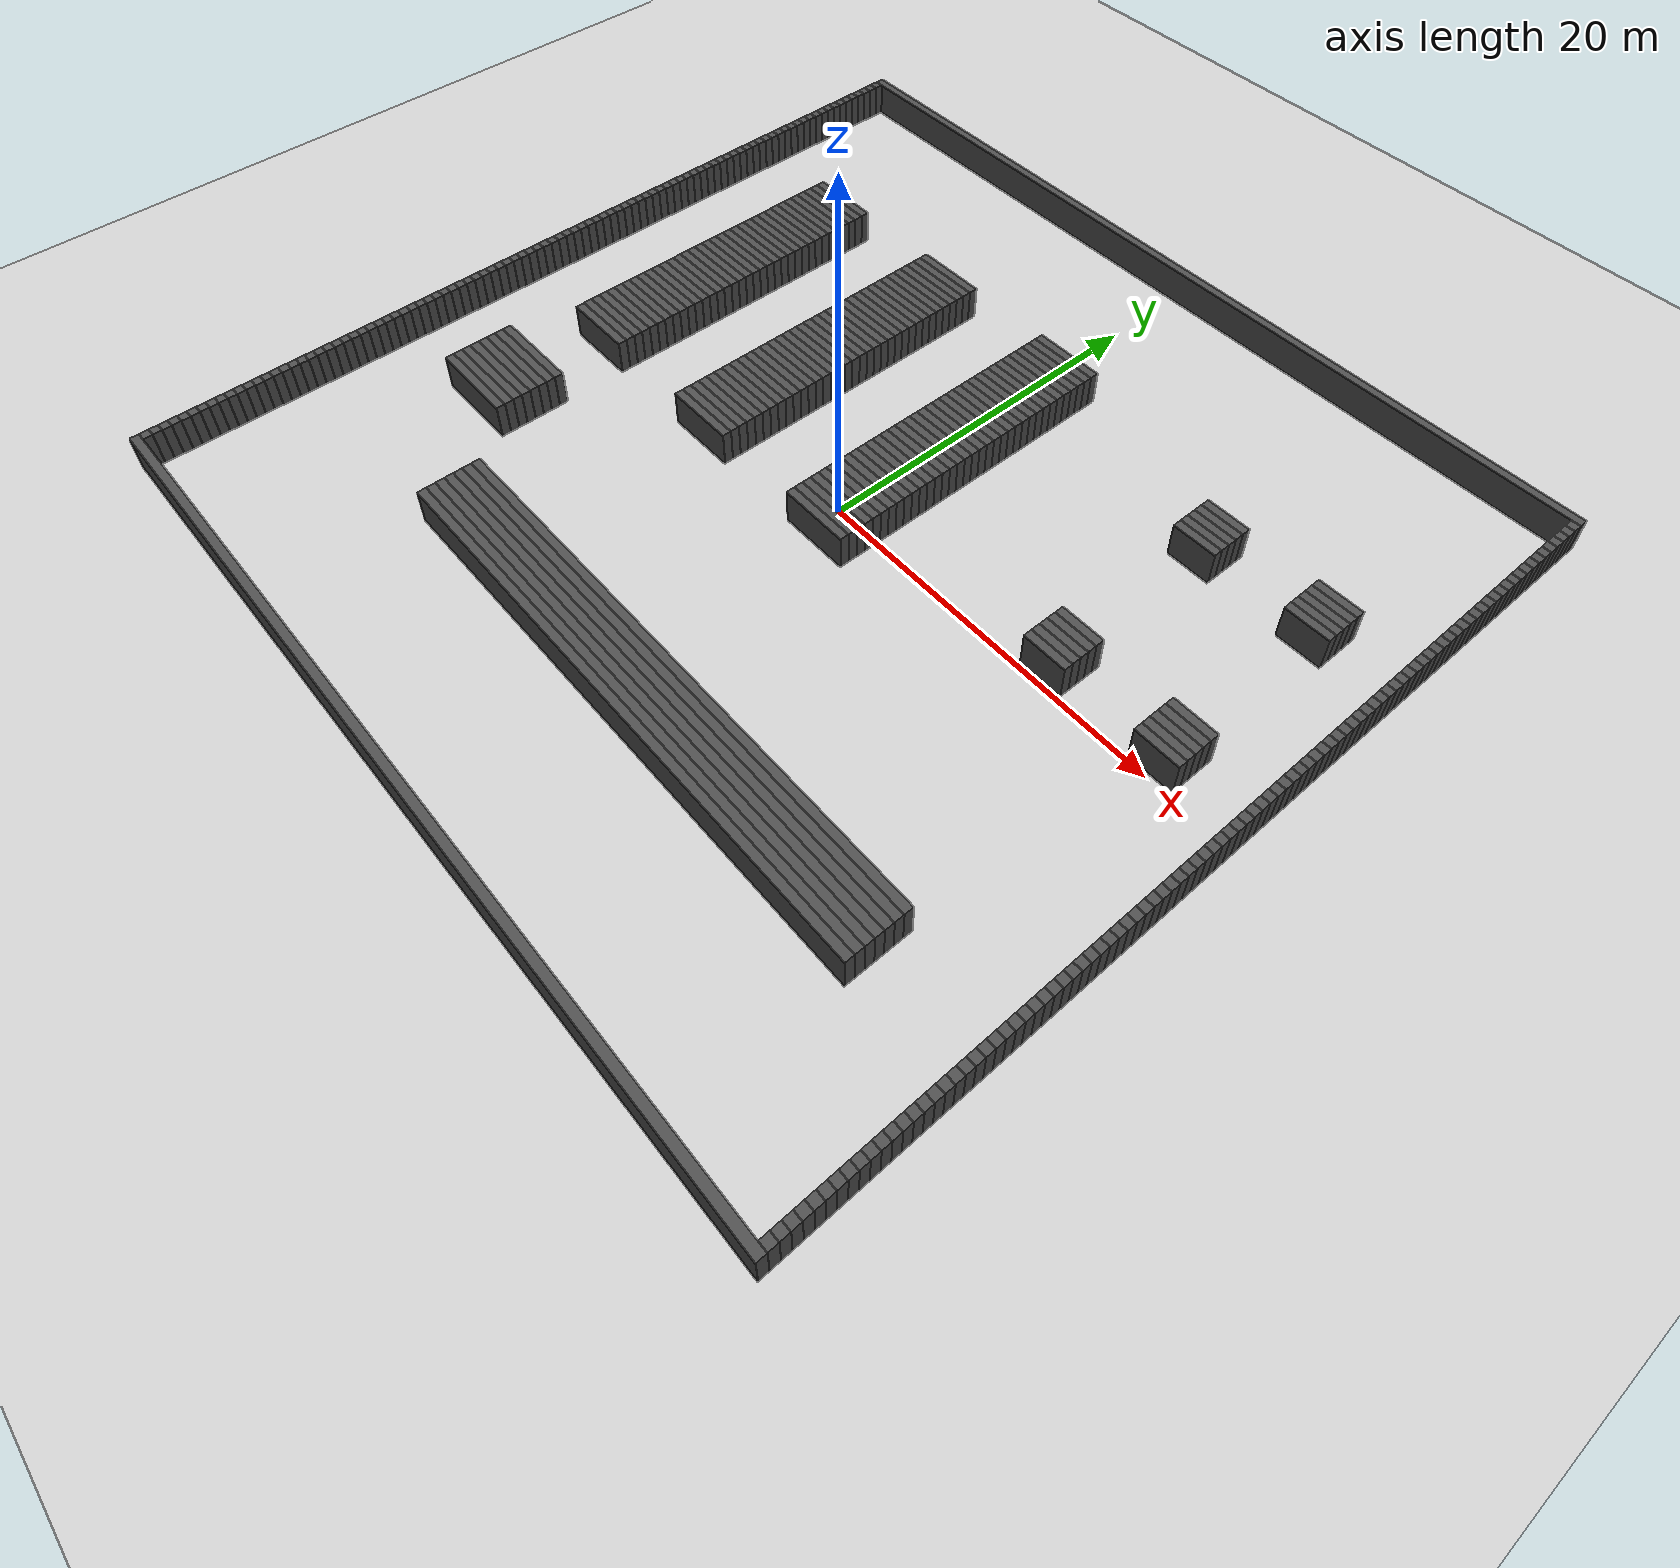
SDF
<?xml version="1.0" ?>
<sdf version="1.6">
  <world name="factory_world">
    <physics name="1ms" type="ignored">
      <max_step_size>0.001</max_step_size>
      <real_time_factor>1.0</real_time_factor>
    </physics>
    <plugin filename="gz-sim-physics-system" name="gz::sim::systems::Physics">
      <engine>
        <filename>gz-physics-dartsim-plugin</filename>
      </engine>
    </plugin>
    <plugin filename="gz-sim-user-commands-system" name="gz::sim::systems::UserCommands"/>
    <plugin filename="gz-sim-scene-broadcaster-system" name="gz::sim::systems::SceneBroadcaster"/>
    <plugin filename="gz-sim-sensors-system" name="gz::sim::systems::Sensors">
      <render_engine>ogre2</render_engine>
    </plugin>

    <light type="directional" name="sun">
      <cast_shadows>true</cast_shadows>
      <pose>0 0 10 0 0 0</pose>
      <diffuse>0.8 0.8 0.8 1</diffuse>
      <specular>0.2 0.2 0.2 1</specular>
      <direction>-0.5 0.1 -0.9</direction>
    </light>

    <model name="ground_plane">
      <static>true</static>
      <link name="link">
        <collision name="collision">
          <geometry><plane><normal>0 0 1</normal><size>50.0 50.0</size></plane></geometry>
        </collision>
        <visual name="visual">
          <geometry><plane><normal>0 0 1</normal><size>50.0 50.0</size></plane></geometry>
          <material><ambient>0.8 0.8 0.8 1</ambient><diffuse>0.8 0.8 0.8 1</diffuse></material>
        </visual>
      </link>
    </model>

    <model name="factory_obstacles">
      <static>true</static>
      <link name="walls_link">

        <collision name="wall_col_0">
          <pose>-0.25 25.0 1.0 0 0 0</pose>
          <geometry><box><size>50.0 0.5 2.0</size></box></geometry>
        </collision>
        <visual name="wall_vis_0">
          <pose>-0.25 25.0 1.0 0 0 0</pose>
          <geometry><box><size>50.0 0.5 2.0</size></box></geometry>
          <material><ambient>0.3 0.3 0.3 1</ambient><diffuse>0.3 0.3 0.3 1</diffuse></material>
        </visual>
        <collision name="wall_col_1">
          <pose>-25.0 24.5 1.0 0 0 0</pose>
          <geometry><box><size>0.5 0.5 2.0</size></box></geometry>
        </collision>
        <visual name="wall_vis_1">
          <pose>-25.0 24.5 1.0 0 0 0</pose>
          <geometry><box><size>0.5 0.5 2.0</size></box></geometry>
          <material><ambient>0.3 0.3 0.3 1</ambient><diffuse>0.3 0.3 0.3 1</diffuse></material>
        </visual>
        <collision name="wall_col_2">
          <pose>24.5 24.5 1.0 0 0 0</pose>
          <geometry><box><size>0.5 0.5 2.0</size></box></geometry>
        </collision>
        <visual name="wall_vis_2">
          <pose>24.5 24.5 1.0 0 0 0</pose>
          <geometry><box><size>0.5 0.5 2.0</size></box></geometry>
          <material><ambient>0.3 0.3 0.3 1</ambient><diffuse>0.3 0.3 0.3 1</diffuse></material>
        </visual>
        <collision name="wall_col_3">
          <pose>-25.0 24.0 1.0 0 0 0</pose>
          <geometry><box><size>0.5 0.5 2.0</size></box></geometry>
        </collision>
        <visual name="wall_vis_3">
          <pose>-25.0 24.0 1.0 0 0 0</pose>
          <geometry><box><size>0.5 0.5 2.0</size></box></geometry>
          <material><ambient>0.3 0.3 0.3 1</ambient><diffuse>0.3 0.3 0.3 1</diffuse></material>
        </visual>
        <collision name="wall_col_4">
          <pose>24.5 24.0 1.0 0 0 0</pose>
          <geometry><box><size>0.5 0.5 2.0</size></box></geometry>
        </collision>
        <visual name="wall_vis_4">
          <pose>24.5 24.0 1.0 0 0 0</pose>
          <geometry><box><size>0.5 0.5 2.0</size></box></geometry>
          <material><ambient>0.3 0.3 0.3 1</ambient><diffuse>0.3 0.3 0.3 1</diffuse></material>
        </visual>
        <collision name="wall_col_5">
          <pose>-25.0 23.5 1.0 0 0 0</pose>
          <geometry><box><size>0.5 0.5 2.0</size></box></geometry>
        </collision>
        <visual name="wall_vis_5">
          <pose>-25.0 23.5 1.0 0 0 0</pose>
          <geometry><box><size>0.5 0.5 2.0</size></box></geometry>
          <material><ambient>0.3 0.3 0.3 1</ambient><diffuse>0.3 0.3 0.3 1</diffuse></material>
        </visual>
        <collision name="wall_col_6">
          <pose>24.5 23.5 1.0 0 0 0</pose>
          <geometry><box><size>0.5 0.5 2.0</size></box></geometry>
        </collision>
        <visual name="wall_vis_6">
          <pose>24.5 23.5 1.0 0 0 0</pose>
          <geometry><box><size>0.5 0.5 2.0</size></box></geometry>
          <material><ambient>0.3 0.3 0.3 1</ambient><diffuse>0.3 0.3 0.3 1</diffuse></material>
        </visual>
        <collision name="wall_col_7">
          <pose>-25.0 23.0 1.0 0 0 0</pose>
          <geometry><box><size>0.5 0.5 2.0</size></box></geometry>
        </collision>
        <visual name="wall_vis_7">
          <pose>-25.0 23.0 1.0 0 0 0</pose>
          <geometry><box><size>0.5 0.5 2.0</size></box></geometry>
          <material><ambient>0.3 0.3 0.3 1</ambient><diffuse>0.3 0.3 0.3 1</diffuse></material>
        </visual>
        <collision name="wall_col_8">
          <pose>24.5 23.0 1.0 0 0 0</pose>
          <geometry><box><size>0.5 0.5 2.0</size></box></geometry>
        </collision>
        <visual name="wall_vis_8">
          <pose>24.5 23.0 1.0 0 0 0</pose>
          <geometry><box><size>0.5 0.5 2.0</size></box></geometry>
          <material><ambient>0.3 0.3 0.3 1</ambient><diffuse>0.3 0.3 0.3 1</diffuse></material>
        </visual>
        <collision name="wall_col_9">
          <pose>-25.0 22.5 1.0 0 0 0</pose>
          <geometry><box><size>0.5 0.5 2.0</size></box></geometry>
        </collision>
        <visual name="wall_vis_9">
          <pose>-25.0 22.5 1.0 0 0 0</pose>
          <geometry><box><size>0.5 0.5 2.0</size></box></geometry>
          <material><ambient>0.3 0.3 0.3 1</ambient><diffuse>0.3 0.3 0.3 1</diffuse></material>
        </visual>
        <collision name="wall_col_10">
          <pose>24.5 22.5 1.0 0 0 0</pose>
          <geometry><box><size>0.5 0.5 2.0</size></box></geometry>
        </collision>
        <visual name="wall_vis_10">
          <pose>24.5 22.5 1.0 0 0 0</pose>
          <geometry><box><size>0.5 0.5 2.0</size></box></geometry>
          <material><ambient>0.3 0.3 0.3 1</ambient><diffuse>0.3 0.3 0.3 1</diffuse></material>
        </visual>
        <collision name="wall_col_11">
          <pose>-25.0 22.0 1.0 0 0 0</pose>
          <geometry><box><size>0.5 0.5 2.0</size></box></geometry>
        </collision>
        <visual name="wall_vis_11">
          <pose>-25.0 22.0 1.0 0 0 0</pose>
          <geometry><box><size>0.5 0.5 2.0</size></box></geometry>
          <material><ambient>0.3 0.3 0.3 1</ambient><diffuse>0.3 0.3 0.3 1</diffuse></material>
        </visual>
        <collision name="wall_col_12">
          <pose>24.5 22.0 1.0 0 0 0</pose>
          <geometry><box><size>0.5 0.5 2.0</size></box></geometry>
        </collision>
        <visual name="wall_vis_12">
          <pose>24.5 22.0 1.0 0 0 0</pose>
          <geometry><box><size>0.5 0.5 2.0</size></box></geometry>
          <material><ambient>0.3 0.3 0.3 1</ambient><diffuse>0.3 0.3 0.3 1</diffuse></material>
        </visual>
        <collision name="wall_col_13">
          <pose>-25.0 21.5 1.0 0 0 0</pose>
          <geometry><box><size>0.5 0.5 2.0</size></box></geometry>
        </collision>
        <visual name="wall_vis_13">
          <pose>-25.0 21.5 1.0 0 0 0</pose>
          <geometry><box><size>0.5 0.5 2.0</size></box></geometry>
          <material><ambient>0.3 0.3 0.3 1</ambient><diffuse>0.3 0.3 0.3 1</diffuse></material>
        </visual>
        <collision name="wall_col_14">
          <pose>24.5 21.5 1.0 0 0 0</pose>
          <geometry><box><size>0.5 0.5 2.0</size></box></geometry>
        </collision>
        <visual name="wall_vis_14">
          <pose>24.5 21.5 1.0 0 0 0</pose>
          <geometry><box><size>0.5 0.5 2.0</size></box></geometry>
          <material><ambient>0.3 0.3 0.3 1</ambient><diffuse>0.3 0.3 0.3 1</diffuse></material>
        </visual>
        <collision name="wall_col_15">
          <pose>-25.0 21.0 1.0 0 0 0</pose>
          <geometry><box><size>0.5 0.5 2.0</size></box></geometry>
        </collision>
        <visual name="wall_vis_15">
          <pose>-25.0 21.0 1.0 0 0 0</pose>
          <geometry><box><size>0.5 0.5 2.0</size></box></geometry>
          <material><ambient>0.3 0.3 0.3 1</ambient><diffuse>0.3 0.3 0.3 1</diffuse></material>
        </visual>
        <collision name="wall_col_16">
          <pose>24.5 21.0 1.0 0 0 0</pose>
          <geometry><box><size>0.5 0.5 2.0</size></box></geometry>
        </collision>
        <visual name="wall_vis_16">
          <pose>24.5 21.0 1.0 0 0 0</pose>
          <geometry><box><size>0.5 0.5 2.0</size></box></geometry>
          <material><ambient>0.3 0.3 0.3 1</ambient><diffuse>0.3 0.3 0.3 1</diffuse></material>
        </visual>
        <collision name="wall_col_17">
          <pose>-25.0 20.5 1.0 0 0 0</pose>
          <geometry><box><size>0.5 0.5 2.0</size></box></geometry>
        </collision>
        <visual name="wall_vis_17">
          <pose>-25.0 20.5 1.0 0 0 0</pose>
          <geometry><box><size>0.5 0.5 2.0</size></box></geometry>
          <material><ambient>0.3 0.3 0.3 1</ambient><diffuse>0.3 0.3 0.3 1</diffuse></material>
        </visual>
        <collision name="wall_col_18">
          <pose>24.5 20.5 1.0 0 0 0</pose>
          <geometry><box><size>0.5 0.5 2.0</size></box></geometry>
        </collision>
        <visual name="wall_vis_18">
          <pose>24.5 20.5 1.0 0 0 0</pose>
          <geometry><box><size>0.5 0.5 2.0</size></box></geometry>
          <material><ambient>0.3 0.3 0.3 1</ambient><diffuse>0.3 0.3 0.3 1</diffuse></material>
        </visual>
        <collision name="wall_col_19">
          <pose>-25.0 20.0 1.0 0 0 0</pose>
          <geometry><box><size>0.5 0.5 2.0</size></box></geometry>
        </collision>
        <visual name="wall_vis_19">
          <pose>-25.0 20.0 1.0 0 0 0</pose>
          <geometry><box><size>0.5 0.5 2.0</size></box></geometry>
          <material><ambient>0.3 0.3 0.3 1</ambient><diffuse>0.3 0.3 0.3 1</diffuse></material>
        </visual>
        <collision name="wall_col_20">
          <pose>24.5 20.0 1.0 0 0 0</pose>
          <geometry><box><size>0.5 0.5 2.0</size></box></geometry>
        </collision>
        <visual name="wall_vis_20">
          <pose>24.5 20.0 1.0 0 0 0</pose>
          <geometry><box><size>0.5 0.5 2.0</size></box></geometry>
          <material><ambient>0.3 0.3 0.3 1</ambient><diffuse>0.3 0.3 0.3 1</diffuse></material>
        </visual>
        <collision name="wall_col_21">
          <pose>-25.0 19.5 1.0 0 0 0</pose>
          <geometry><box><size>0.5 0.5 2.0</size></box></geometry>
        </collision>
        <visual name="wall_vis_21">
          <pose>-25.0 19.5 1.0 0 0 0</pose>
          <geometry><box><size>0.5 0.5 2.0</size></box></geometry>
          <material><ambient>0.3 0.3 0.3 1</ambient><diffuse>0.3 0.3 0.3 1</diffuse></material>
        </visual>
        <collision name="wall_col_22">
          <pose>24.5 19.5 1.0 0 0 0</pose>
          <geometry><box><size>0.5 0.5 2.0</size></box></geometry>
        </collision>
        <visual name="wall_vis_22">
          <pose>24.5 19.5 1.0 0 0 0</pose>
          <geometry><box><size>0.5 0.5 2.0</size></box></geometry>
          <material><ambient>0.3 0.3 0.3 1</ambient><diffuse>0.3 0.3 0.3 1</diffuse></material>
        </visual>
        <collision name="wall_col_23">
          <pose>-25.0 19.0 1.0 0 0 0</pose>
          <geometry><box><size>0.5 0.5 2.0</size></box></geometry>
        </collision>
        <visual name="wall_vis_23">
          <pose>-25.0 19.0 1.0 0 0 0</pose>
          <geometry><box><size>0.5 0.5 2.0</size></box></geometry>
          <material><ambient>0.3 0.3 0.3 1</ambient><diffuse>0.3 0.3 0.3 1</diffuse></material>
        </visual>
        <collision name="wall_col_24">
          <pose>24.5 19.0 1.0 0 0 0</pose>
          <geometry><box><size>0.5 0.5 2.0</size></box></geometry>
        </collision>
        <visual name="wall_vis_24">
          <pose>24.5 19.0 1.0 0 0 0</pose>
          <geometry><box><size>0.5 0.5 2.0</size></box></geometry>
          <material><ambient>0.3 0.3 0.3 1</ambient><diffuse>0.3 0.3 0.3 1</diffuse></material>
        </visual>
        <collision name="wall_col_25">
          <pose>-25.0 18.5 1.0 0 0 0</pose>
          <geometry><box><size>0.5 0.5 2.0</size></box></geometry>
        </collision>
        <visual name="wall_vis_25">
          <pose>-25.0 18.5 1.0 0 0 0</pose>
          <geometry><box><size>0.5 0.5 2.0</size></box></geometry>
          <material><ambient>0.3 0.3 0.3 1</ambient><diffuse>0.3 0.3 0.3 1</diffuse></material>
        </visual>
        <collision name="wall_col_26">
          <pose>24.5 18.5 1.0 0 0 0</pose>
          <geometry><box><size>0.5 0.5 2.0</size></box></geometry>
        </collision>
        <visual name="wall_vis_26">
          <pose>24.5 18.5 1.0 0 0 0</pose>
          <geometry><box><size>0.5 0.5 2.0</size></box></geometry>
          <material><ambient>0.3 0.3 0.3 1</ambient><diffuse>0.3 0.3 0.3 1</diffuse></material>
        </visual>
        <collision name="wall_col_27">
          <pose>-25.0 18.0 1.0 0 0 0</pose>
          <geometry><box><size>0.5 0.5 2.0</size></box></geometry>
        </collision>
        <visual name="wall_vis_27">
          <pose>-25.0 18.0 1.0 0 0 0</pose>
          <geometry><box><size>0.5 0.5 2.0</size></box></geometry>
          <material><ambient>0.3 0.3 0.3 1</ambient><diffuse>0.3 0.3 0.3 1</diffuse></material>
        </visual>
        <collision name="wall_col_28">
          <pose>24.5 18.0 1.0 0 0 0</pose>
          <geometry><box><size>0.5 0.5 2.0</size></box></geometry>
        </collision>
        <visual name="wall_vis_28">
          <pose>24.5 18.0 1.0 0 0 0</pose>
          <geometry><box><size>0.5 0.5 2.0</size></box></geometry>
          <material><ambient>0.3 0.3 0.3 1</ambient><diffuse>0.3 0.3 0.3 1</diffuse></material>
        </visual>
        <collision name="wall_col_29">
          <pose>-25.0 17.5 1.0 0 0 0</pose>
          <geometry><box><size>0.5 0.5 2.0</size></box></geometry>
        </collision>
        <visual name="wall_vis_29">
          <pose>-25.0 17.5 1.0 0 0 0</pose>
          <geometry><box><size>0.5 0.5 2.0</size></box></geometry>
          <material><ambient>0.3 0.3 0.3 1</ambient><diffuse>0.3 0.3 0.3 1</diffuse></material>
        </visual>
        <collision name="wall_col_30">
          <pose>24.5 17.5 1.0 0 0 0</pose>
          <geometry><box><size>0.5 0.5 2.0</size></box></geometry>
        </collision>
        <visual name="wall_vis_30">
          <pose>24.5 17.5 1.0 0 0 0</pose>
          <geometry><box><size>0.5 0.5 2.0</size></box></geometry>
          <material><ambient>0.3 0.3 0.3 1</ambient><diffuse>0.3 0.3 0.3 1</diffuse></material>
        </visual>
        <collision name="wall_col_31">
          <pose>-25.0 17.0 1.0 0 0 0</pose>
          <geometry><box><size>0.5 0.5 2.0</size></box></geometry>
        </collision>
        <visual name="wall_vis_31">
          <pose>-25.0 17.0 1.0 0 0 0</pose>
          <geometry><box><size>0.5 0.5 2.0</size></box></geometry>
          <material><ambient>0.3 0.3 0.3 1</ambient><diffuse>0.3 0.3 0.3 1</diffuse></material>
        </visual>
        <collision name="wall_col_32">
          <pose>24.5 17.0 1.0 0 0 0</pose>
          <geometry><box><size>0.5 0.5 2.0</size></box></geometry>
        </collision>
        <visual name="wall_vis_32">
          <pose>24.5 17.0 1.0 0 0 0</pose>
          <geometry><box><size>0.5 0.5 2.0</size></box></geometry>
          <material><ambient>0.3 0.3 0.3 1</ambient><diffuse>0.3 0.3 0.3 1</diffuse></material>
        </visual>
        <collision name="wall_col_33">
          <pose>-25.0 16.5 1.0 0 0 0</pose>
          <geometry><box><size>0.5 0.5 2.0</size></box></geometry>
        </collision>
        <visual name="wall_vis_33">
          <pose>-25.0 16.5 1.0 0 0 0</pose>
          <geometry><box><size>0.5 0.5 2.0</size></box></geometry>
          <material><ambient>0.3 0.3 0.3 1</ambient><diffuse>0.3 0.3 0.3 1</diffuse></material>
        </visual>
        <collision name="wall_col_34">
          <pose>24.5 16.5 1.0 0 0 0</pose>
          <geometry><box><size>0.5 0.5 2.0</size></box></geometry>
        </collision>
        <visual name="wall_vis_34">
          <pose>24.5 16.5 1.0 0 0 0</pose>
          <geometry><box><size>0.5 0.5 2.0</size></box></geometry>
          <material><ambient>0.3 0.3 0.3 1</ambient><diffuse>0.3 0.3 0.3 1</diffuse></material>
        </visual>
        <collision name="wall_col_35">
          <pose>-25.0 16.0 1.0 0 0 0</pose>
          <geometry><box><size>0.5 0.5 2.0</size></box></geometry>
        </collision>
        <visual name="wall_vis_35">
          <pose>-25.0 16.0 1.0 0 0 0</pose>
          <geometry><box><size>0.5 0.5 2.0</size></box></geometry>
          <material><ambient>0.3 0.3 0.3 1</ambient><diffuse>0.3 0.3 0.3 1</diffuse></material>
        </visual>
        <collision name="wall_col_36">
          <pose>24.5 16.0 1.0 0 0 0</pose>
          <geometry><box><size>0.5 0.5 2.0</size></box></geometry>
        </collision>
        <visual name="wall_vis_36">
          <pose>24.5 16.0 1.0 0 0 0</pose>
          <geometry><box><size>0.5 0.5 2.0</size></box></geometry>
          <material><ambient>0.3 0.3 0.3 1</ambient><diffuse>0.3 0.3 0.3 1</diffuse></material>
        </visual>
        <collision name="wall_col_37">
          <pose>-25.0 15.5 1.0 0 0 0</pose>
          <geometry><box><size>0.5 0.5 2.0</size></box></geometry>
        </collision>
        <visual name="wall_vis_37">
          <pose>-25.0 15.5 1.0 0 0 0</pose>
          <geometry><box><size>0.5 0.5 2.0</size></box></geometry>
          <material><ambient>0.3 0.3 0.3 1</ambient><diffuse>0.3 0.3 0.3 1</diffuse></material>
        </visual>
        <collision name="wall_col_38">
          <pose>24.5 15.5 1.0 0 0 0</pose>
          <geometry><box><size>0.5 0.5 2.0</size></box></geometry>
        </collision>
        <visual name="wall_vis_38">
          <pose>24.5 15.5 1.0 0 0 0</pose>
          <geometry><box><size>0.5 0.5 2.0</size></box></geometry>
          <material><ambient>0.3 0.3 0.3 1</ambient><diffuse>0.3 0.3 0.3 1</diffuse></material>
        </visual>
        <collision name="wall_col_39">
          <pose>-25.0 15.0 1.0 0 0 0</pose>
          <geometry><box><size>0.5 0.5 2.0</size></box></geometry>
        </collision>
        <visual name="wall_vis_39">
          <pose>-25.0 15.0 1.0 0 0 0</pose>
          <geometry><box><size>0.5 0.5 2.0</size></box></geometry>
          <material><ambient>0.3 0.3 0.3 1</ambient><diffuse>0.3 0.3 0.3 1</diffuse></material>
        </visual>
        <collision name="wall_col_40">
          <pose>-17.25 15.0 1.0 0 0 0</pose>
          <geometry><box><size>4.0 0.5 2.0</size></box></geometry>
        </collision>
        <visual name="wall_vis_40">
          <pose>-17.25 15.0 1.0 0 0 0</pose>
          <geometry><box><size>4.0 0.5 2.0</size></box></geometry>
          <material><ambient>0.3 0.3 0.3 1</ambient><diffuse>0.3 0.3 0.3 1</diffuse></material>
        </visual>
        <collision name="wall_col_41">
          <pose>-8.25 15.0 1.0 0 0 0</pose>
          <geometry><box><size>4.0 0.5 2.0</size></box></geometry>
        </collision>
        <visual name="wall_vis_41">
          <pose>-8.25 15.0 1.0 0 0 0</pose>
          <geometry><box><size>4.0 0.5 2.0</size></box></geometry>
          <material><ambient>0.3 0.3 0.3 1</ambient><diffuse>0.3 0.3 0.3 1</diffuse></material>
        </visual>
        <collision name="wall_col_42">
          <pose>0.75 15.0 1.0 0 0 0</pose>
          <geometry><box><size>4.0 0.5 2.0</size></box></geometry>
        </collision>
        <visual name="wall_vis_42">
          <pose>0.75 15.0 1.0 0 0 0</pose>
          <geometry><box><size>4.0 0.5 2.0</size></box></geometry>
          <material><ambient>0.3 0.3 0.3 1</ambient><diffuse>0.3 0.3 0.3 1</diffuse></material>
        </visual>
        <collision name="wall_col_43">
          <pose>24.5 15.0 1.0 0 0 0</pose>
          <geometry><box><size>0.5 0.5 2.0</size></box></geometry>
        </collision>
        <visual name="wall_vis_43">
          <pose>24.5 15.0 1.0 0 0 0</pose>
          <geometry><box><size>0.5 0.5 2.0</size></box></geometry>
          <material><ambient>0.3 0.3 0.3 1</ambient><diffuse>0.3 0.3 0.3 1</diffuse></material>
        </visual>
        <collision name="wall_col_44">
          <pose>-25.0 14.5 1.0 0 0 0</pose>
          <geometry><box><size>0.5 0.5 2.0</size></box></geometry>
        </collision>
        <visual name="wall_vis_44">
          <pose>-25.0 14.5 1.0 0 0 0</pose>
          <geometry><box><size>0.5 0.5 2.0</size></box></geometry>
          <material><ambient>0.3 0.3 0.3 1</ambient><diffuse>0.3 0.3 0.3 1</diffuse></material>
        </visual>
        <collision name="wall_col_45">
          <pose>-17.25 14.5 1.0 0 0 0</pose>
          <geometry><box><size>4.0 0.5 2.0</size></box></geometry>
        </collision>
        <visual name="wall_vis_45">
          <pose>-17.25 14.5 1.0 0 0 0</pose>
          <geometry><box><size>4.0 0.5 2.0</size></box></geometry>
          <material><ambient>0.3 0.3 0.3 1</ambient><diffuse>0.3 0.3 0.3 1</diffuse></material>
        </visual>
        <collision name="wall_col_46">
          <pose>-8.25 14.5 1.0 0 0 0</pose>
          <geometry><box><size>4.0 0.5 2.0</size></box></geometry>
        </collision>
        <visual name="wall_vis_46">
          <pose>-8.25 14.5 1.0 0 0 0</pose>
          <geometry><box><size>4.0 0.5 2.0</size></box></geometry>
          <material><ambient>0.3 0.3 0.3 1</ambient><diffuse>0.3 0.3 0.3 1</diffuse></material>
        </visual>
        <collision name="wall_col_47">
          <pose>0.75 14.5 1.0 0 0 0</pose>
          <geometry><box><size>4.0 0.5 2.0</size></box></geometry>
        </collision>
        <visual name="wall_vis_47">
          <pose>0.75 14.5 1.0 0 0 0</pose>
          <geometry><box><size>4.0 0.5 2.0</size></box></geometry>
          <material><ambient>0.3 0.3 0.3 1</ambient><diffuse>0.3 0.3 0.3 1</diffuse></material>
        </visual>
        <collision name="wall_col_48">
          <pose>24.5 14.5 1.0 0 0 0</pose>
          <geometry><box><size>0.5 0.5 2.0</size></box></geometry>
        </collision>
        <visual name="wall_vis_48">
          <pose>24.5 14.5 1.0 0 0 0</pose>
          <geometry><box><size>0.5 0.5 2.0</size></box></geometry>
          <material><ambient>0.3 0.3 0.3 1</ambient><diffuse>0.3 0.3 0.3 1</diffuse></material>
        </visual>
        <collision name="wall_col_49">
          <pose>-25.0 14.0 1.0 0 0 0</pose>
          <geometry><box><size>0.5 0.5 2.0</size></box></geometry>
        </collision>
        <visual name="wall_vis_49">
          <pose>-25.0 14.0 1.0 0 0 0</pose>
          <geometry><box><size>0.5 0.5 2.0</size></box></geometry>
          <material><ambient>0.3 0.3 0.3 1</ambient><diffuse>0.3 0.3 0.3 1</diffuse></material>
        </visual>
        <collision name="wall_col_50">
          <pose>-17.25 14.0 1.0 0 0 0</pose>
          <geometry><box><size>4.0 0.5 2.0</size></box></geometry>
        </collision>
        <visual name="wall_vis_50">
          <pose>-17.25 14.0 1.0 0 0 0</pose>
          <geometry><box><size>4.0 0.5 2.0</size></box></geometry>
          <material><ambient>0.3 0.3 0.3 1</ambient><diffuse>0.3 0.3 0.3 1</diffuse></material>
        </visual>
        <collision name="wall_col_51">
          <pose>-8.25 14.0 1.0 0 0 0</pose>
          <geometry><box><size>4.0 0.5 2.0</size></box></geometry>
        </collision>
        <visual name="wall_vis_51">
          <pose>-8.25 14.0 1.0 0 0 0</pose>
          <geometry><box><size>4.0 0.5 2.0</size></box></geometry>
          <material><ambient>0.3 0.3 0.3 1</ambient><diffuse>0.3 0.3 0.3 1</diffuse></material>
        </visual>
        <collision name="wall_col_52">
          <pose>0.75 14.0 1.0 0 0 0</pose>
          <geometry><box><size>4.0 0.5 2.0</size></box></geometry>
        </collision>
        <visual name="wall_vis_52">
          <pose>0.75 14.0 1.0 0 0 0</pose>
          <geometry><box><size>4.0 0.5 2.0</size></box></geometry>
          <material><ambient>0.3 0.3 0.3 1</ambient><diffuse>0.3 0.3 0.3 1</diffuse></material>
        </visual>
        <collision name="wall_col_53">
          <pose>24.5 14.0 1.0 0 0 0</pose>
          <geometry><box><size>0.5 0.5 2.0</size></box></geometry>
        </collision>
        <visual name="wall_vis_53">
          <pose>24.5 14.0 1.0 0 0 0</pose>
          <geometry><box><size>0.5 0.5 2.0</size></box></geometry>
          <material><ambient>0.3 0.3 0.3 1</ambient><diffuse>0.3 0.3 0.3 1</diffuse></material>
        </visual>
        <collision name="wall_col_54">
          <pose>-25.0 13.5 1.0 0 0 0</pose>
          <geometry><box><size>0.5 0.5 2.0</size></box></geometry>
        </collision>
        <visual name="wall_vis_54">
          <pose>-25.0 13.5 1.0 0 0 0</pose>
          <geometry><box><size>0.5 0.5 2.0</size></box></geometry>
          <material><ambient>0.3 0.3 0.3 1</ambient><diffuse>0.3 0.3 0.3 1</diffuse></material>
        </visual>
        <collision name="wall_col_55">
          <pose>-17.25 13.5 1.0 0 0 0</pose>
          <geometry><box><size>4.0 0.5 2.0</size></box></geometry>
        </collision>
        <visual name="wall_vis_55">
          <pose>-17.25 13.5 1.0 0 0 0</pose>
          <geometry><box><size>4.0 0.5 2.0</size></box></geometry>
          <material><ambient>0.3 0.3 0.3 1</ambient><diffuse>0.3 0.3 0.3 1</diffuse></material>
        </visual>
        <collision name="wall_col_56">
          <pose>-8.25 13.5 1.0 0 0 0</pose>
          <geometry><box><size>4.0 0.5 2.0</size></box></geometry>
        </collision>
        <visual name="wall_vis_56">
          <pose>-8.25 13.5 1.0 0 0 0</pose>
          <geometry><box><size>4.0 0.5 2.0</size></box></geometry>
          <material><ambient>0.3 0.3 0.3 1</ambient><diffuse>0.3 0.3 0.3 1</diffuse></material>
        </visual>
        <collision name="wall_col_57">
          <pose>0.75 13.5 1.0 0 0 0</pose>
          <geometry><box><size>4.0 0.5 2.0</size></box></geometry>
        </collision>
        <visual name="wall_vis_57">
          <pose>0.75 13.5 1.0 0 0 0</pose>
          <geometry><box><size>4.0 0.5 2.0</size></box></geometry>
          <material><ambient>0.3 0.3 0.3 1</ambient><diffuse>0.3 0.3 0.3 1</diffuse></material>
        </visual>
        <collision name="wall_col_58">
          <pose>24.5 13.5 1.0 0 0 0</pose>
          <geometry><box><size>0.5 0.5 2.0</size></box></geometry>
        </collision>
        <visual name="wall_vis_58">
          <pose>24.5 13.5 1.0 0 0 0</pose>
          <geometry><box><size>0.5 0.5 2.0</size></box></geometry>
          <material><ambient>0.3 0.3 0.3 1</ambient><diffuse>0.3 0.3 0.3 1</diffuse></material>
        </visual>
        <collision name="wall_col_59">
          <pose>-25.0 13.0 1.0 0 0 0</pose>
          <geometry><box><size>0.5 0.5 2.0</size></box></geometry>
        </collision>
        <visual name="wall_vis_59">
          <pose>-25.0 13.0 1.0 0 0 0</pose>
          <geometry><box><size>0.5 0.5 2.0</size></box></geometry>
          <material><ambient>0.3 0.3 0.3 1</ambient><diffuse>0.3 0.3 0.3 1</diffuse></material>
        </visual>
        <collision name="wall_col_60">
          <pose>-17.25 13.0 1.0 0 0 0</pose>
          <geometry><box><size>4.0 0.5 2.0</size></box></geometry>
        </collision>
        <visual name="wall_vis_60">
          <pose>-17.25 13.0 1.0 0 0 0</pose>
          <geometry><box><size>4.0 0.5 2.0</size></box></geometry>
          <material><ambient>0.3 0.3 0.3 1</ambient><diffuse>0.3 0.3 0.3 1</diffuse></material>
        </visual>
        <collision name="wall_col_61">
          <pose>-8.25 13.0 1.0 0 0 0</pose>
          <geometry><box><size>4.0 0.5 2.0</size></box></geometry>
        </collision>
        <visual name="wall_vis_61">
          <pose>-8.25 13.0 1.0 0 0 0</pose>
          <geometry><box><size>4.0 0.5 2.0</size></box></geometry>
          <material><ambient>0.3 0.3 0.3 1</ambient><diffuse>0.3 0.3 0.3 1</diffuse></material>
        </visual>
        <collision name="wall_col_62">
          <pose>0.75 13.0 1.0 0 0 0</pose>
          <geometry><box><size>4.0 0.5 2.0</size></box></geometry>
        </collision>
        <visual name="wall_vis_62">
          <pose>0.75 13.0 1.0 0 0 0</pose>
          <geometry><box><size>4.0 0.5 2.0</size></box></geometry>
          <material><ambient>0.3 0.3 0.3 1</ambient><diffuse>0.3 0.3 0.3 1</diffuse></material>
        </visual>
        <collision name="wall_col_63">
          <pose>24.5 13.0 1.0 0 0 0</pose>
          <geometry><box><size>0.5 0.5 2.0</size></box></geometry>
        </collision>
        <visual name="wall_vis_63">
          <pose>24.5 13.0 1.0 0 0 0</pose>
          <geometry><box><size>0.5 0.5 2.0</size></box></geometry>
          <material><ambient>0.3 0.3 0.3 1</ambient><diffuse>0.3 0.3 0.3 1</diffuse></material>
        </visual>
        <collision name="wall_col_64">
          <pose>-25.0 12.5 1.0 0 0 0</pose>
          <geometry><box><size>0.5 0.5 2.0</size></box></geometry>
        </collision>
        <visual name="wall_vis_64">
          <pose>-25.0 12.5 1.0 0 0 0</pose>
          <geometry><box><size>0.5 0.5 2.0</size></box></geometry>
          <material><ambient>0.3 0.3 0.3 1</ambient><diffuse>0.3 0.3 0.3 1</diffuse></material>
        </visual>
        <collision name="wall_col_65">
          <pose>-17.25 12.5 1.0 0 0 0</pose>
          <geometry><box><size>4.0 0.5 2.0</size></box></geometry>
        </collision>
        <visual name="wall_vis_65">
          <pose>-17.25 12.5 1.0 0 0 0</pose>
          <geometry><box><size>4.0 0.5 2.0</size></box></geometry>
          <material><ambient>0.3 0.3 0.3 1</ambient><diffuse>0.3 0.3 0.3 1</diffuse></material>
        </visual>
        <collision name="wall_col_66">
          <pose>-8.25 12.5 1.0 0 0 0</pose>
          <geometry><box><size>4.0 0.5 2.0</size></box></geometry>
        </collision>
        <visual name="wall_vis_66">
          <pose>-8.25 12.5 1.0 0 0 0</pose>
          <geometry><box><size>4.0 0.5 2.0</size></box></geometry>
          <material><ambient>0.3 0.3 0.3 1</ambient><diffuse>0.3 0.3 0.3 1</diffuse></material>
        </visual>
        <collision name="wall_col_67">
          <pose>0.75 12.5 1.0 0 0 0</pose>
          <geometry><box><size>4.0 0.5 2.0</size></box></geometry>
        </collision>
        <visual name="wall_vis_67">
          <pose>0.75 12.5 1.0 0 0 0</pose>
          <geometry><box><size>4.0 0.5 2.0</size></box></geometry>
          <material><ambient>0.3 0.3 0.3 1</ambient><diffuse>0.3 0.3 0.3 1</diffuse></material>
        </visual>
        <collision name="wall_col_68">
          <pose>13.5 12.5 1.0 0 0 0</pose>
          <geometry><box><size>2.5 0.5 2.0</size></box></geometry>
        </collision>
        <visual name="wall_vis_68">
          <pose>13.5 12.5 1.0 0 0 0</pose>
          <geometry><box><size>2.5 0.5 2.0</size></box></geometry>
          <material><ambient>0.3 0.3 0.3 1</ambient><diffuse>0.3 0.3 0.3 1</diffuse></material>
        </visual>
        <collision name="wall_col_69">
          <pose>20.0 12.5 1.0 0 0 0</pose>
          <geometry><box><size>2.5 0.5 2.0</size></box></geometry>
        </collision>
        <visual name="wall_vis_69">
          <pose>20.0 12.5 1.0 0 0 0</pose>
          <geometry><box><size>2.5 0.5 2.0</size></box></geometry>
          <material><ambient>0.3 0.3 0.3 1</ambient><diffuse>0.3 0.3 0.3 1</diffuse></material>
        </visual>
        <collision name="wall_col_70">
          <pose>24.5 12.5 1.0 0 0 0</pose>
          <geometry><box><size>0.5 0.5 2.0</size></box></geometry>
        </collision>
        <visual name="wall_vis_70">
          <pose>24.5 12.5 1.0 0 0 0</pose>
          <geometry><box><size>0.5 0.5 2.0</size></box></geometry>
          <material><ambient>0.3 0.3 0.3 1</ambient><diffuse>0.3 0.3 0.3 1</diffuse></material>
        </visual>
        <collision name="wall_col_71">
          <pose>-25.0 12.0 1.0 0 0 0</pose>
          <geometry><box><size>0.5 0.5 2.0</size></box></geometry>
        </collision>
        <visual name="wall_vis_71">
          <pose>-25.0 12.0 1.0 0 0 0</pose>
          <geometry><box><size>0.5 0.5 2.0</size></box></geometry>
          <material><ambient>0.3 0.3 0.3 1</ambient><diffuse>0.3 0.3 0.3 1</diffuse></material>
        </visual>
        <collision name="wall_col_72">
          <pose>-17.25 12.0 1.0 0 0 0</pose>
          <geometry><box><size>4.0 0.5 2.0</size></box></geometry>
        </collision>
        <visual name="wall_vis_72">
          <pose>-17.25 12.0 1.0 0 0 0</pose>
          <geometry><box><size>4.0 0.5 2.0</size></box></geometry>
          <material><ambient>0.3 0.3 0.3 1</ambient><diffuse>0.3 0.3 0.3 1</diffuse></material>
        </visual>
        <collision name="wall_col_73">
          <pose>-8.25 12.0 1.0 0 0 0</pose>
          <geometry><box><size>4.0 0.5 2.0</size></box></geometry>
        </collision>
        <visual name="wall_vis_73">
          <pose>-8.25 12.0 1.0 0 0 0</pose>
          <geometry><box><size>4.0 0.5 2.0</size></box></geometry>
          <material><ambient>0.3 0.3 0.3 1</ambient><diffuse>0.3 0.3 0.3 1</diffuse></material>
        </visual>
        <collision name="wall_col_74">
          <pose>0.75 12.0 1.0 0 0 0</pose>
          <geometry><box><size>4.0 0.5 2.0</size></box></geometry>
        </collision>
        <visual name="wall_vis_74">
          <pose>0.75 12.0 1.0 0 0 0</pose>
          <geometry><box><size>4.0 0.5 2.0</size></box></geometry>
          <material><ambient>0.3 0.3 0.3 1</ambient><diffuse>0.3 0.3 0.3 1</diffuse></material>
        </visual>
        <collision name="wall_col_75">
          <pose>13.5 12.0 1.0 0 0 0</pose>
          <geometry><box><size>2.5 0.5 2.0</size></box></geometry>
        </collision>
        <visual name="wall_vis_75">
          <pose>13.5 12.0 1.0 0 0 0</pose>
          <geometry><box><size>2.5 0.5 2.0</size></box></geometry>
          <material><ambient>0.3 0.3 0.3 1</ambient><diffuse>0.3 0.3 0.3 1</diffuse></material>
        </visual>
        <collision name="wall_col_76">
          <pose>20.0 12.0 1.0 0 0 0</pose>
          <geometry><box><size>2.5 0.5 2.0</size></box></geometry>
        </collision>
        <visual name="wall_vis_76">
          <pose>20.0 12.0 1.0 0 0 0</pose>
          <geometry><box><size>2.5 0.5 2.0</size></box></geometry>
          <material><ambient>0.3 0.3 0.3 1</ambient><diffuse>0.3 0.3 0.3 1</diffuse></material>
        </visual>
        <collision name="wall_col_77">
          <pose>24.5 12.0 1.0 0 0 0</pose>
          <geometry><box><size>0.5 0.5 2.0</size></box></geometry>
        </collision>
        <visual name="wall_vis_77">
          <pose>24.5 12.0 1.0 0 0 0</pose>
          <geometry><box><size>0.5 0.5 2.0</size></box></geometry>
          <material><ambient>0.3 0.3 0.3 1</ambient><diffuse>0.3 0.3 0.3 1</diffuse></material>
        </visual>
        <collision name="wall_col_78">
          <pose>-25.0 11.5 1.0 0 0 0</pose>
          <geometry><box><size>0.5 0.5 2.0</size></box></geometry>
        </collision>
        <visual name="wall_vis_78">
          <pose>-25.0 11.5 1.0 0 0 0</pose>
          <geometry><box><size>0.5 0.5 2.0</size></box></geometry>
          <material><ambient>0.3 0.3 0.3 1</ambient><diffuse>0.3 0.3 0.3 1</diffuse></material>
        </visual>
        <collision name="wall_col_79">
          <pose>-17.25 11.5 1.0 0 0 0</pose>
          <geometry><box><size>4.0 0.5 2.0</size></box></geometry>
        </collision>
        <visual name="wall_vis_79">
          <pose>-17.25 11.5 1.0 0 0 0</pose>
          <geometry><box><size>4.0 0.5 2.0</size></box></geometry>
          <material><ambient>0.3 0.3 0.3 1</ambient><diffuse>0.3 0.3 0.3 1</diffuse></material>
        </visual>
        <collision name="wall_col_80">
          <pose>-8.25 11.5 1.0 0 0 0</pose>
          <geometry><box><size>4.0 0.5 2.0</size></box></geometry>
        </collision>
        <visual name="wall_vis_80">
          <pose>-8.25 11.5 1.0 0 0 0</pose>
          <geometry><box><size>4.0 0.5 2.0</size></box></geometry>
          <material><ambient>0.3 0.3 0.3 1</ambient><diffuse>0.3 0.3 0.3 1</diffuse></material>
        </visual>
        <collision name="wall_col_81">
          <pose>0.75 11.5 1.0 0 0 0</pose>
          <geometry><box><size>4.0 0.5 2.0</size></box></geometry>
        </collision>
        <visual name="wall_vis_81">
          <pose>0.75 11.5 1.0 0 0 0</pose>
          <geometry><box><size>4.0 0.5 2.0</size></box></geometry>
          <material><ambient>0.3 0.3 0.3 1</ambient><diffuse>0.3 0.3 0.3 1</diffuse></material>
        </visual>
        <collision name="wall_col_82">
          <pose>13.5 11.5 1.0 0 0 0</pose>
          <geometry><box><size>2.5 0.5 2.0</size></box></geometry>
        </collision>
        <visual name="wall_vis_82">
          <pose>13.5 11.5 1.0 0 0 0</pose>
          <geometry><box><size>2.5 0.5 2.0</size></box></geometry>
          <material><ambient>0.3 0.3 0.3 1</ambient><diffuse>0.3 0.3 0.3 1</diffuse></material>
        </visual>
        <collision name="wall_col_83">
          <pose>20.0 11.5 1.0 0 0 0</pose>
          <geometry><box><size>2.5 0.5 2.0</size></box></geometry>
        </collision>
        <visual name="wall_vis_83">
          <pose>20.0 11.5 1.0 0 0 0</pose>
          <geometry><box><size>2.5 0.5 2.0</size></box></geometry>
          <material><ambient>0.3 0.3 0.3 1</ambient><diffuse>0.3 0.3 0.3 1</diffuse></material>
        </visual>
        <collision name="wall_col_84">
          <pose>24.5 11.5 1.0 0 0 0</pose>
          <geometry><box><size>0.5 0.5 2.0</size></box></geometry>
        </collision>
        <visual name="wall_vis_84">
          <pose>24.5 11.5 1.0 0 0 0</pose>
          <geometry><box><size>0.5 0.5 2.0</size></box></geometry>
          <material><ambient>0.3 0.3 0.3 1</ambient><diffuse>0.3 0.3 0.3 1</diffuse></material>
        </visual>
        <collision name="wall_col_85">
          <pose>-25.0 11.0 1.0 0 0 0</pose>
          <geometry><box><size>0.5 0.5 2.0</size></box></geometry>
        </collision>
        <visual name="wall_vis_85">
          <pose>-25.0 11.0 1.0 0 0 0</pose>
          <geometry><box><size>0.5 0.5 2.0</size></box></geometry>
          <material><ambient>0.3 0.3 0.3 1</ambient><diffuse>0.3 0.3 0.3 1</diffuse></material>
        </visual>
        <collision name="wall_col_86">
          <pose>-17.25 11.0 1.0 0 0 0</pose>
          <geometry><box><size>4.0 0.5 2.0</size></box></geometry>
        </collision>
        <visual name="wall_vis_86">
          <pose>-17.25 11.0 1.0 0 0 0</pose>
          <geometry><box><size>4.0 0.5 2.0</size></box></geometry>
          <material><ambient>0.3 0.3 0.3 1</ambient><diffuse>0.3 0.3 0.3 1</diffuse></material>
        </visual>
        <collision name="wall_col_87">
          <pose>-8.25 11.0 1.0 0 0 0</pose>
          <geometry><box><size>4.0 0.5 2.0</size></box></geometry>
        </collision>
        <visual name="wall_vis_87">
          <pose>-8.25 11.0 1.0 0 0 0</pose>
          <geometry><box><size>4.0 0.5 2.0</size></box></geometry>
          <material><ambient>0.3 0.3 0.3 1</ambient><diffuse>0.3 0.3 0.3 1</diffuse></material>
        </visual>
        <collision name="wall_col_88">
          <pose>0.75 11.0 1.0 0 0 0</pose>
          <geometry><box><size>4.0 0.5 2.0</size></box></geometry>
        </collision>
        <visual name="wall_vis_88">
          <pose>0.75 11.0 1.0 0 0 0</pose>
          <geometry><box><size>4.0 0.5 2.0</size></box></geometry>
          <material><ambient>0.3 0.3 0.3 1</ambient><diffuse>0.3 0.3 0.3 1</diffuse></material>
        </visual>
        <collision name="wall_col_89">
          <pose>13.5 11.0 1.0 0 0 0</pose>
          <geometry><box><size>2.5 0.5 2.0</size></box></geometry>
        </collision>
        <visual name="wall_vis_89">
          <pose>13.5 11.0 1.0 0 0 0</pose>
          <geometry><box><size>2.5 0.5 2.0</size></box></geometry>
          <material><ambient>0.3 0.3 0.3 1</ambient><diffuse>0.3 0.3 0.3 1</diffuse></material>
        </visual>
        <collision name="wall_col_90">
          <pose>20.0 11.0 1.0 0 0 0</pose>
          <geometry><box><size>2.5 0.5 2.0</size></box></geometry>
        </collision>
        <visual name="wall_vis_90">
          <pose>20.0 11.0 1.0 0 0 0</pose>
          <geometry><box><size>2.5 0.5 2.0</size></box></geometry>
          <material><ambient>0.3 0.3 0.3 1</ambient><diffuse>0.3 0.3 0.3 1</diffuse></material>
        </visual>
        <collision name="wall_col_91">
          <pose>24.5 11.0 1.0 0 0 0</pose>
          <geometry><box><size>0.5 0.5 2.0</size></box></geometry>
        </collision>
        <visual name="wall_vis_91">
          <pose>24.5 11.0 1.0 0 0 0</pose>
          <geometry><box><size>0.5 0.5 2.0</size></box></geometry>
          <material><ambient>0.3 0.3 0.3 1</ambient><diffuse>0.3 0.3 0.3 1</diffuse></material>
        </visual>
        <collision name="wall_col_92">
          <pose>-25.0 10.5 1.0 0 0 0</pose>
          <geometry><box><size>0.5 0.5 2.0</size></box></geometry>
        </collision>
        <visual name="wall_vis_92">
          <pose>-25.0 10.5 1.0 0 0 0</pose>
          <geometry><box><size>0.5 0.5 2.0</size></box></geometry>
          <material><ambient>0.3 0.3 0.3 1</ambient><diffuse>0.3 0.3 0.3 1</diffuse></material>
        </visual>
        <collision name="wall_col_93">
          <pose>-17.25 10.5 1.0 0 0 0</pose>
          <geometry><box><size>4.0 0.5 2.0</size></box></geometry>
        </collision>
        <visual name="wall_vis_93">
          <pose>-17.25 10.5 1.0 0 0 0</pose>
          <geometry><box><size>4.0 0.5 2.0</size></box></geometry>
          <material><ambient>0.3 0.3 0.3 1</ambient><diffuse>0.3 0.3 0.3 1</diffuse></material>
        </visual>
        <collision name="wall_col_94">
          <pose>-8.25 10.5 1.0 0 0 0</pose>
          <geometry><box><size>4.0 0.5 2.0</size></box></geometry>
        </collision>
        <visual name="wall_vis_94">
          <pose>-8.25 10.5 1.0 0 0 0</pose>
          <geometry><box><size>4.0 0.5 2.0</size></box></geometry>
          <material><ambient>0.3 0.3 0.3 1</ambient><diffuse>0.3 0.3 0.3 1</diffuse></material>
        </visual>
        <collision name="wall_col_95">
          <pose>0.75 10.5 1.0 0 0 0</pose>
          <geometry><box><size>4.0 0.5 2.0</size></box></geometry>
        </collision>
        <visual name="wall_vis_95">
          <pose>0.75 10.5 1.0 0 0 0</pose>
          <geometry><box><size>4.0 0.5 2.0</size></box></geometry>
          <material><ambient>0.3 0.3 0.3 1</ambient><diffuse>0.3 0.3 0.3 1</diffuse></material>
        </visual>
        <collision name="wall_col_96">
          <pose>13.5 10.5 1.0 0 0 0</pose>
          <geometry><box><size>2.5 0.5 2.0</size></box></geometry>
        </collision>
        <visual name="wall_vis_96">
          <pose>13.5 10.5 1.0 0 0 0</pose>
          <geometry><box><size>2.5 0.5 2.0</size></box></geometry>
          <material><ambient>0.3 0.3 0.3 1</ambient><diffuse>0.3 0.3 0.3 1</diffuse></material>
        </visual>
        <collision name="wall_col_97">
          <pose>20.0 10.5 1.0 0 0 0</pose>
          <geometry><box><size>2.5 0.5 2.0</size></box></geometry>
        </collision>
        <visual name="wall_vis_97">
          <pose>20.0 10.5 1.0 0 0 0</pose>
          <geometry><box><size>2.5 0.5 2.0</size></box></geometry>
          <material><ambient>0.3 0.3 0.3 1</ambient><diffuse>0.3 0.3 0.3 1</diffuse></material>
        </visual>
        <collision name="wall_col_98">
          <pose>24.5 10.5 1.0 0 0 0</pose>
          <geometry><box><size>0.5 0.5 2.0</size></box></geometry>
        </collision>
        <visual name="wall_vis_98">
          <pose>24.5 10.5 1.0 0 0 0</pose>
          <geometry><box><size>0.5 0.5 2.0</size></box></geometry>
          <material><ambient>0.3 0.3 0.3 1</ambient><diffuse>0.3 0.3 0.3 1</diffuse></material>
        </visual>
        <collision name="wall_col_99">
          <pose>-25.0 10.0 1.0 0 0 0</pose>
          <geometry><box><size>0.5 0.5 2.0</size></box></geometry>
        </collision>
        <visual name="wall_vis_99">
          <pose>-25.0 10.0 1.0 0 0 0</pose>
          <geometry><box><size>0.5 0.5 2.0</size></box></geometry>
          <material><ambient>0.3 0.3 0.3 1</ambient><diffuse>0.3 0.3 0.3 1</diffuse></material>
        </visual>
        <collision name="wall_col_100">
          <pose>-17.25 10.0 1.0 0 0 0</pose>
          <geometry><box><size>4.0 0.5 2.0</size></box></geometry>
        </collision>
        <visual name="wall_vis_100">
          <pose>-17.25 10.0 1.0 0 0 0</pose>
          <geometry><box><size>4.0 0.5 2.0</size></box></geometry>
          <material><ambient>0.3 0.3 0.3 1</ambient><diffuse>0.3 0.3 0.3 1</diffuse></material>
        </visual>
        <collision name="wall_col_101">
          <pose>-8.25 10.0 1.0 0 0 0</pose>
          <geometry><box><size>4.0 0.5 2.0</size></box></geometry>
        </collision>
        <visual name="wall_vis_101">
          <pose>-8.25 10.0 1.0 0 0 0</pose>
          <geometry><box><size>4.0 0.5 2.0</size></box></geometry>
          <material><ambient>0.3 0.3 0.3 1</ambient><diffuse>0.3 0.3 0.3 1</diffuse></material>
        </visual>
        <collision name="wall_col_102">
          <pose>0.75 10.0 1.0 0 0 0</pose>
          <geometry><box><size>4.0 0.5 2.0</size></box></geometry>
        </collision>
        <visual name="wall_vis_102">
          <pose>0.75 10.0 1.0 0 0 0</pose>
          <geometry><box><size>4.0 0.5 2.0</size></box></geometry>
          <material><ambient>0.3 0.3 0.3 1</ambient><diffuse>0.3 0.3 0.3 1</diffuse></material>
        </visual>
        <collision name="wall_col_103">
          <pose>24.5 10.0 1.0 0 0 0</pose>
          <geometry><box><size>0.5 0.5 2.0</size></box></geometry>
        </collision>
        <visual name="wall_vis_103">
          <pose>24.5 10.0 1.0 0 0 0</pose>
          <geometry><box><size>0.5 0.5 2.0</size></box></geometry>
          <material><ambient>0.3 0.3 0.3 1</ambient><diffuse>0.3 0.3 0.3 1</diffuse></material>
        </visual>
        <collision name="wall_col_104">
          <pose>-25.0 9.5 1.0 0 0 0</pose>
          <geometry><box><size>0.5 0.5 2.0</size></box></geometry>
        </collision>
        <visual name="wall_vis_104">
          <pose>-25.0 9.5 1.0 0 0 0</pose>
          <geometry><box><size>0.5 0.5 2.0</size></box></geometry>
          <material><ambient>0.3 0.3 0.3 1</ambient><diffuse>0.3 0.3 0.3 1</diffuse></material>
        </visual>
        <collision name="wall_col_105">
          <pose>-17.25 9.5 1.0 0 0 0</pose>
          <geometry><box><size>4.0 0.5 2.0</size></box></geometry>
        </collision>
        <visual name="wall_vis_105">
          <pose>-17.25 9.5 1.0 0 0 0</pose>
          <geometry><box><size>4.0 0.5 2.0</size></box></geometry>
          <material><ambient>0.3 0.3 0.3 1</ambient><diffuse>0.3 0.3 0.3 1</diffuse></material>
        </visual>
        <collision name="wall_col_106">
          <pose>-8.25 9.5 1.0 0 0 0</pose>
          <geometry><box><size>4.0 0.5 2.0</size></box></geometry>
        </collision>
        <visual name="wall_vis_106">
          <pose>-8.25 9.5 1.0 0 0 0</pose>
          <geometry><box><size>4.0 0.5 2.0</size></box></geometry>
          <material><ambient>0.3 0.3 0.3 1</ambient><diffuse>0.3 0.3 0.3 1</diffuse></material>
        </visual>
        <collision name="wall_col_107">
          <pose>0.75 9.5 1.0 0 0 0</pose>
          <geometry><box><size>4.0 0.5 2.0</size></box></geometry>
        </collision>
        <visual name="wall_vis_107">
          <pose>0.75 9.5 1.0 0 0 0</pose>
          <geometry><box><size>4.0 0.5 2.0</size></box></geometry>
          <material><ambient>0.3 0.3 0.3 1</ambient><diffuse>0.3 0.3 0.3 1</diffuse></material>
        </visual>
        <collision name="wall_col_108">
          <pose>24.5 9.5 1.0 0 0 0</pose>
          <geometry><box><size>0.5 0.5 2.0</size></box></geometry>
        </collision>
        <visual name="wall_vis_108">
          <pose>24.5 9.5 1.0 0 0 0</pose>
          <geometry><box><size>0.5 0.5 2.0</size></box></geometry>
          <material><ambient>0.3 0.3 0.3 1</ambient><diffuse>0.3 0.3 0.3 1</diffuse></material>
        </visual>
        <collision name="wall_col_109">
          <pose>-25.0 9.0 1.0 0 0 0</pose>
          <geometry><box><size>0.5 0.5 2.0</size></box></geometry>
        </collision>
        <visual name="wall_vis_109">
          <pose>-25.0 9.0 1.0 0 0 0</pose>
          <geometry><box><size>0.5 0.5 2.0</size></box></geometry>
          <material><ambient>0.3 0.3 0.3 1</ambient><diffuse>0.3 0.3 0.3 1</diffuse></material>
        </visual>
        <collision name="wall_col_110">
          <pose>-17.25 9.0 1.0 0 0 0</pose>
          <geometry><box><size>4.0 0.5 2.0</size></box></geometry>
        </collision>
        <visual name="wall_vis_110">
          <pose>-17.25 9.0 1.0 0 0 0</pose>
          <geometry><box><size>4.0 0.5 2.0</size></box></geometry>
          <material><ambient>0.3 0.3 0.3 1</ambient><diffuse>0.3 0.3 0.3 1</diffuse></material>
        </visual>
        <collision name="wall_col_111">
          <pose>-8.25 9.0 1.0 0 0 0</pose>
          <geometry><box><size>4.0 0.5 2.0</size></box></geometry>
        </collision>
        <visual name="wall_vis_111">
          <pose>-8.25 9.0 1.0 0 0 0</pose>
          <geometry><box><size>4.0 0.5 2.0</size></box></geometry>
          <material><ambient>0.3 0.3 0.3 1</ambient><diffuse>0.3 0.3 0.3 1</diffuse></material>
        </visual>
        <collision name="wall_col_112">
          <pose>0.75 9.0 1.0 0 0 0</pose>
          <geometry><box><size>4.0 0.5 2.0</size></box></geometry>
        </collision>
        <visual name="wall_vis_112">
          <pose>0.75 9.0 1.0 0 0 0</pose>
          <geometry><box><size>4.0 0.5 2.0</size></box></geometry>
          <material><ambient>0.3 0.3 0.3 1</ambient><diffuse>0.3 0.3 0.3 1</diffuse></material>
        </visual>
        <collision name="wall_col_113">
          <pose>24.5 9.0 1.0 0 0 0</pose>
          <geometry><box><size>0.5 0.5 2.0</size></box></geometry>
        </collision>
        <visual name="wall_vis_113">
          <pose>24.5 9.0 1.0 0 0 0</pose>
          <geometry><box><size>0.5 0.5 2.0</size></box></geometry>
          <material><ambient>0.3 0.3 0.3 1</ambient><diffuse>0.3 0.3 0.3 1</diffuse></material>
        </visual>
        <collision name="wall_col_114">
          <pose>-25.0 8.5 1.0 0 0 0</pose>
          <geometry><box><size>0.5 0.5 2.0</size></box></geometry>
        </collision>
        <visual name="wall_vis_114">
          <pose>-25.0 8.5 1.0 0 0 0</pose>
          <geometry><box><size>0.5 0.5 2.0</size></box></geometry>
          <material><ambient>0.3 0.3 0.3 1</ambient><diffuse>0.3 0.3 0.3 1</diffuse></material>
        </visual>
        <collision name="wall_col_115">
          <pose>-17.25 8.5 1.0 0 0 0</pose>
          <geometry><box><size>4.0 0.5 2.0</size></box></geometry>
        </collision>
        <visual name="wall_vis_115">
          <pose>-17.25 8.5 1.0 0 0 0</pose>
          <geometry><box><size>4.0 0.5 2.0</size></box></geometry>
          <material><ambient>0.3 0.3 0.3 1</ambient><diffuse>0.3 0.3 0.3 1</diffuse></material>
        </visual>
        <collision name="wall_col_116">
          <pose>-8.25 8.5 1.0 0 0 0</pose>
          <geometry><box><size>4.0 0.5 2.0</size></box></geometry>
        </collision>
        <visual name="wall_vis_116">
          <pose>-8.25 8.5 1.0 0 0 0</pose>
          <geometry><box><size>4.0 0.5 2.0</size></box></geometry>
          <material><ambient>0.3 0.3 0.3 1</ambient><diffuse>0.3 0.3 0.3 1</diffuse></material>
        </visual>
        <collision name="wall_col_117">
          <pose>0.75 8.5 1.0 0 0 0</pose>
          <geometry><box><size>4.0 0.5 2.0</size></box></geometry>
        </collision>
        <visual name="wall_vis_117">
          <pose>0.75 8.5 1.0 0 0 0</pose>
          <geometry><box><size>4.0 0.5 2.0</size></box></geometry>
          <material><ambient>0.3 0.3 0.3 1</ambient><diffuse>0.3 0.3 0.3 1</diffuse></material>
        </visual>
        <collision name="wall_col_118">
          <pose>24.5 8.5 1.0 0 0 0</pose>
          <geometry><box><size>0.5 0.5 2.0</size></box></geometry>
        </collision>
        <visual name="wall_vis_118">
          <pose>24.5 8.5 1.0 0 0 0</pose>
          <geometry><box><size>0.5 0.5 2.0</size></box></geometry>
          <material><ambient>0.3 0.3 0.3 1</ambient><diffuse>0.3 0.3 0.3 1</diffuse></material>
        </visual>
        <collision name="wall_col_119">
          <pose>-25.0 8.0 1.0 0 0 0</pose>
          <geometry><box><size>0.5 0.5 2.0</size></box></geometry>
        </collision>
        <visual name="wall_vis_119">
          <pose>-25.0 8.0 1.0 0 0 0</pose>
          <geometry><box><size>0.5 0.5 2.0</size></box></geometry>
          <material><ambient>0.3 0.3 0.3 1</ambient><diffuse>0.3 0.3 0.3 1</diffuse></material>
        </visual>
        <collision name="wall_col_120">
          <pose>-17.25 8.0 1.0 0 0 0</pose>
          <geometry><box><size>4.0 0.5 2.0</size></box></geometry>
        </collision>
        <visual name="wall_vis_120">
          <pose>-17.25 8.0 1.0 0 0 0</pose>
          <geometry><box><size>4.0 0.5 2.0</size></box></geometry>
          <material><ambient>0.3 0.3 0.3 1</ambient><diffuse>0.3 0.3 0.3 1</diffuse></material>
        </visual>
        <collision name="wall_col_121">
          <pose>-8.25 8.0 1.0 0 0 0</pose>
          <geometry><box><size>4.0 0.5 2.0</size></box></geometry>
        </collision>
        <visual name="wall_vis_121">
          <pose>-8.25 8.0 1.0 0 0 0</pose>
          <geometry><box><size>4.0 0.5 2.0</size></box></geometry>
          <material><ambient>0.3 0.3 0.3 1</ambient><diffuse>0.3 0.3 0.3 1</diffuse></material>
        </visual>
        <collision name="wall_col_122">
          <pose>0.75 8.0 1.0 0 0 0</pose>
          <geometry><box><size>4.0 0.5 2.0</size></box></geometry>
        </collision>
        <visual name="wall_vis_122">
          <pose>0.75 8.0 1.0 0 0 0</pose>
          <geometry><box><size>4.0 0.5 2.0</size></box></geometry>
          <material><ambient>0.3 0.3 0.3 1</ambient><diffuse>0.3 0.3 0.3 1</diffuse></material>
        </visual>
        <collision name="wall_col_123">
          <pose>24.5 8.0 1.0 0 0 0</pose>
          <geometry><box><size>0.5 0.5 2.0</size></box></geometry>
        </collision>
        <visual name="wall_vis_123">
          <pose>24.5 8.0 1.0 0 0 0</pose>
          <geometry><box><size>0.5 0.5 2.0</size></box></geometry>
          <material><ambient>0.3 0.3 0.3 1</ambient><diffuse>0.3 0.3 0.3 1</diffuse></material>
        </visual>
        <collision name="wall_col_124">
          <pose>-25.0 7.5 1.0 0 0 0</pose>
          <geometry><box><size>0.5 0.5 2.0</size></box></geometry>
        </collision>
        <visual name="wall_vis_124">
          <pose>-25.0 7.5 1.0 0 0 0</pose>
          <geometry><box><size>0.5 0.5 2.0</size></box></geometry>
          <material><ambient>0.3 0.3 0.3 1</ambient><diffuse>0.3 0.3 0.3 1</diffuse></material>
        </visual>
        <collision name="wall_col_125">
          <pose>-17.25 7.5 1.0 0 0 0</pose>
          <geometry><box><size>4.0 0.5 2.0</size></box></geometry>
        </collision>
        <visual name="wall_vis_125">
          <pose>-17.25 7.5 1.0 0 0 0</pose>
          <geometry><box><size>4.0 0.5 2.0</size></box></geometry>
          <material><ambient>0.3 0.3 0.3 1</ambient><diffuse>0.3 0.3 0.3 1</diffuse></material>
        </visual>
        <collision name="wall_col_126">
          <pose>-8.25 7.5 1.0 0 0 0</pose>
          <geometry><box><size>4.0 0.5 2.0</size></box></geometry>
        </collision>
        <visual name="wall_vis_126">
          <pose>-8.25 7.5 1.0 0 0 0</pose>
          <geometry><box><size>4.0 0.5 2.0</size></box></geometry>
          <material><ambient>0.3 0.3 0.3 1</ambient><diffuse>0.3 0.3 0.3 1</diffuse></material>
        </visual>
        <collision name="wall_col_127">
          <pose>0.75 7.5 1.0 0 0 0</pose>
          <geometry><box><size>4.0 0.5 2.0</size></box></geometry>
        </collision>
        <visual name="wall_vis_127">
          <pose>0.75 7.5 1.0 0 0 0</pose>
          <geometry><box><size>4.0 0.5 2.0</size></box></geometry>
          <material><ambient>0.3 0.3 0.3 1</ambient><diffuse>0.3 0.3 0.3 1</diffuse></material>
        </visual>
        <collision name="wall_col_128">
          <pose>24.5 7.5 1.0 0 0 0</pose>
          <geometry><box><size>0.5 0.5 2.0</size></box></geometry>
        </collision>
        <visual name="wall_vis_128">
          <pose>24.5 7.5 1.0 0 0 0</pose>
          <geometry><box><size>0.5 0.5 2.0</size></box></geometry>
          <material><ambient>0.3 0.3 0.3 1</ambient><diffuse>0.3 0.3 0.3 1</diffuse></material>
        </visual>
        <collision name="wall_col_129">
          <pose>-25.0 7.0 1.0 0 0 0</pose>
          <geometry><box><size>0.5 0.5 2.0</size></box></geometry>
        </collision>
        <visual name="wall_vis_129">
          <pose>-25.0 7.0 1.0 0 0 0</pose>
          <geometry><box><size>0.5 0.5 2.0</size></box></geometry>
          <material><ambient>0.3 0.3 0.3 1</ambient><diffuse>0.3 0.3 0.3 1</diffuse></material>
        </visual>
        <collision name="wall_col_130">
          <pose>-17.25 7.0 1.0 0 0 0</pose>
          <geometry><box><size>4.0 0.5 2.0</size></box></geometry>
        </collision>
        <visual name="wall_vis_130">
          <pose>-17.25 7.0 1.0 0 0 0</pose>
          <geometry><box><size>4.0 0.5 2.0</size></box></geometry>
          <material><ambient>0.3 0.3 0.3 1</ambient><diffuse>0.3 0.3 0.3 1</diffuse></material>
        </visual>
        <collision name="wall_col_131">
          <pose>-8.25 7.0 1.0 0 0 0</pose>
          <geometry><box><size>4.0 0.5 2.0</size></box></geometry>
        </collision>
        <visual name="wall_vis_131">
          <pose>-8.25 7.0 1.0 0 0 0</pose>
          <geometry><box><size>4.0 0.5 2.0</size></box></geometry>
          <material><ambient>0.3 0.3 0.3 1</ambient><diffuse>0.3 0.3 0.3 1</diffuse></material>
        </visual>
        <collision name="wall_col_132">
          <pose>0.75 7.0 1.0 0 0 0</pose>
          <geometry><box><size>4.0 0.5 2.0</size></box></geometry>
        </collision>
        <visual name="wall_vis_132">
          <pose>0.75 7.0 1.0 0 0 0</pose>
          <geometry><box><size>4.0 0.5 2.0</size></box></geometry>
          <material><ambient>0.3 0.3 0.3 1</ambient><diffuse>0.3 0.3 0.3 1</diffuse></material>
        </visual>
        <collision name="wall_col_133">
          <pose>24.5 7.0 1.0 0 0 0</pose>
          <geometry><box><size>0.5 0.5 2.0</size></box></geometry>
        </collision>
        <visual name="wall_vis_133">
          <pose>24.5 7.0 1.0 0 0 0</pose>
          <geometry><box><size>0.5 0.5 2.0</size></box></geometry>
          <material><ambient>0.3 0.3 0.3 1</ambient><diffuse>0.3 0.3 0.3 1</diffuse></material>
        </visual>
        <collision name="wall_col_134">
          <pose>-25.0 6.5 1.0 0 0 0</pose>
          <geometry><box><size>0.5 0.5 2.0</size></box></geometry>
        </collision>
        <visual name="wall_vis_134">
          <pose>-25.0 6.5 1.0 0 0 0</pose>
          <geometry><box><size>0.5 0.5 2.0</size></box></geometry>
          <material><ambient>0.3 0.3 0.3 1</ambient><diffuse>0.3 0.3 0.3 1</diffuse></material>
        </visual>
        <collision name="wall_col_135">
          <pose>-17.25 6.5 1.0 0 0 0</pose>
          <geometry><box><size>4.0 0.5 2.0</size></box></geometry>
        </collision>
        <visual name="wall_vis_135">
          <pose>-17.25 6.5 1.0 0 0 0</pose>
          <geometry><box><size>4.0 0.5 2.0</size></box></geometry>
          <material><ambient>0.3 0.3 0.3 1</ambient><diffuse>0.3 0.3 0.3 1</diffuse></material>
        </visual>
        <collision name="wall_col_136">
          <pose>-8.25 6.5 1.0 0 0 0</pose>
          <geometry><box><size>4.0 0.5 2.0</size></box></geometry>
        </collision>
        <visual name="wall_vis_136">
          <pose>-8.25 6.5 1.0 0 0 0</pose>
          <geometry><box><size>4.0 0.5 2.0</size></box></geometry>
          <material><ambient>0.3 0.3 0.3 1</ambient><diffuse>0.3 0.3 0.3 1</diffuse></material>
        </visual>
        <collision name="wall_col_137">
          <pose>0.75 6.5 1.0 0 0 0</pose>
          <geometry><box><size>4.0 0.5 2.0</size></box></geometry>
        </collision>
        <visual name="wall_vis_137">
          <pose>0.75 6.5 1.0 0 0 0</pose>
          <geometry><box><size>4.0 0.5 2.0</size></box></geometry>
          <material><ambient>0.3 0.3 0.3 1</ambient><diffuse>0.3 0.3 0.3 1</diffuse></material>
        </visual>
        <collision name="wall_col_138">
          <pose>24.5 6.5 1.0 0 0 0</pose>
          <geometry><box><size>0.5 0.5 2.0</size></box></geometry>
        </collision>
        <visual name="wall_vis_138">
          <pose>24.5 6.5 1.0 0 0 0</pose>
          <geometry><box><size>0.5 0.5 2.0</size></box></geometry>
          <material><ambient>0.3 0.3 0.3 1</ambient><diffuse>0.3 0.3 0.3 1</diffuse></material>
        </visual>
        <collision name="wall_col_139">
          <pose>-25.0 6.0 1.0 0 0 0</pose>
          <geometry><box><size>0.5 0.5 2.0</size></box></geometry>
        </collision>
        <visual name="wall_vis_139">
          <pose>-25.0 6.0 1.0 0 0 0</pose>
          <geometry><box><size>0.5 0.5 2.0</size></box></geometry>
          <material><ambient>0.3 0.3 0.3 1</ambient><diffuse>0.3 0.3 0.3 1</diffuse></material>
        </visual>
        <collision name="wall_col_140">
          <pose>-17.25 6.0 1.0 0 0 0</pose>
          <geometry><box><size>4.0 0.5 2.0</size></box></geometry>
        </collision>
        <visual name="wall_vis_140">
          <pose>-17.25 6.0 1.0 0 0 0</pose>
          <geometry><box><size>4.0 0.5 2.0</size></box></geometry>
          <material><ambient>0.3 0.3 0.3 1</ambient><diffuse>0.3 0.3 0.3 1</diffuse></material>
        </visual>
        <collision name="wall_col_141">
          <pose>-8.25 6.0 1.0 0 0 0</pose>
          <geometry><box><size>4.0 0.5 2.0</size></box></geometry>
        </collision>
        <visual name="wall_vis_141">
          <pose>-8.25 6.0 1.0 0 0 0</pose>
          <geometry><box><size>4.0 0.5 2.0</size></box></geometry>
          <material><ambient>0.3 0.3 0.3 1</ambient><diffuse>0.3 0.3 0.3 1</diffuse></material>
        </visual>
        <collision name="wall_col_142">
          <pose>0.75 6.0 1.0 0 0 0</pose>
          <geometry><box><size>4.0 0.5 2.0</size></box></geometry>
        </collision>
        <visual name="wall_vis_142">
          <pose>0.75 6.0 1.0 0 0 0</pose>
          <geometry><box><size>4.0 0.5 2.0</size></box></geometry>
          <material><ambient>0.3 0.3 0.3 1</ambient><diffuse>0.3 0.3 0.3 1</diffuse></material>
        </visual>
        <collision name="wall_col_143">
          <pose>24.5 6.0 1.0 0 0 0</pose>
          <geometry><box><size>0.5 0.5 2.0</size></box></geometry>
        </collision>
        <visual name="wall_vis_143">
          <pose>24.5 6.0 1.0 0 0 0</pose>
          <geometry><box><size>0.5 0.5 2.0</size></box></geometry>
          <material><ambient>0.3 0.3 0.3 1</ambient><diffuse>0.3 0.3 0.3 1</diffuse></material>
        </visual>
        <collision name="wall_col_144">
          <pose>-25.0 5.5 1.0 0 0 0</pose>
          <geometry><box><size>0.5 0.5 2.0</size></box></geometry>
        </collision>
        <visual name="wall_vis_144">
          <pose>-25.0 5.5 1.0 0 0 0</pose>
          <geometry><box><size>0.5 0.5 2.0</size></box></geometry>
          <material><ambient>0.3 0.3 0.3 1</ambient><diffuse>0.3 0.3 0.3 1</diffuse></material>
        </visual>
        <collision name="wall_col_145">
          <pose>-17.25 5.5 1.0 0 0 0</pose>
          <geometry><box><size>4.0 0.5 2.0</size></box></geometry>
        </collision>
        <visual name="wall_vis_145">
          <pose>-17.25 5.5 1.0 0 0 0</pose>
          <geometry><box><size>4.0 0.5 2.0</size></box></geometry>
          <material><ambient>0.3 0.3 0.3 1</ambient><diffuse>0.3 0.3 0.3 1</diffuse></material>
        </visual>
        <collision name="wall_col_146">
          <pose>-8.25 5.5 1.0 0 0 0</pose>
          <geometry><box><size>4.0 0.5 2.0</size></box></geometry>
        </collision>
        <visual name="wall_vis_146">
          <pose>-8.25 5.5 1.0 0 0 0</pose>
          <geometry><box><size>4.0 0.5 2.0</size></box></geometry>
          <material><ambient>0.3 0.3 0.3 1</ambient><diffuse>0.3 0.3 0.3 1</diffuse></material>
        </visual>
        <collision name="wall_col_147">
          <pose>0.75 5.5 1.0 0 0 0</pose>
          <geometry><box><size>4.0 0.5 2.0</size></box></geometry>
        </collision>
        <visual name="wall_vis_147">
          <pose>0.75 5.5 1.0 0 0 0</pose>
          <geometry><box><size>4.0 0.5 2.0</size></box></geometry>
          <material><ambient>0.3 0.3 0.3 1</ambient><diffuse>0.3 0.3 0.3 1</diffuse></material>
        </visual>
        <collision name="wall_col_148">
          <pose>24.5 5.5 1.0 0 0 0</pose>
          <geometry><box><size>0.5 0.5 2.0</size></box></geometry>
        </collision>
        <visual name="wall_vis_148">
          <pose>24.5 5.5 1.0 0 0 0</pose>
          <geometry><box><size>0.5 0.5 2.0</size></box></geometry>
          <material><ambient>0.3 0.3 0.3 1</ambient><diffuse>0.3 0.3 0.3 1</diffuse></material>
        </visual>
        <collision name="wall_col_149">
          <pose>-25.0 5.0 1.0 0 0 0</pose>
          <geometry><box><size>0.5 0.5 2.0</size></box></geometry>
        </collision>
        <visual name="wall_vis_149">
          <pose>-25.0 5.0 1.0 0 0 0</pose>
          <geometry><box><size>0.5 0.5 2.0</size></box></geometry>
          <material><ambient>0.3 0.3 0.3 1</ambient><diffuse>0.3 0.3 0.3 1</diffuse></material>
        </visual>
        <collision name="wall_col_150">
          <pose>-17.25 5.0 1.0 0 0 0</pose>
          <geometry><box><size>4.0 0.5 2.0</size></box></geometry>
        </collision>
        <visual name="wall_vis_150">
          <pose>-17.25 5.0 1.0 0 0 0</pose>
          <geometry><box><size>4.0 0.5 2.0</size></box></geometry>
          <material><ambient>0.3 0.3 0.3 1</ambient><diffuse>0.3 0.3 0.3 1</diffuse></material>
        </visual>
        <collision name="wall_col_151">
          <pose>-8.25 5.0 1.0 0 0 0</pose>
          <geometry><box><size>4.0 0.5 2.0</size></box></geometry>
        </collision>
        <visual name="wall_vis_151">
          <pose>-8.25 5.0 1.0 0 0 0</pose>
          <geometry><box><size>4.0 0.5 2.0</size></box></geometry>
          <material><ambient>0.3 0.3 0.3 1</ambient><diffuse>0.3 0.3 0.3 1</diffuse></material>
        </visual>
        <collision name="wall_col_152">
          <pose>0.75 5.0 1.0 0 0 0</pose>
          <geometry><box><size>4.0 0.5 2.0</size></box></geometry>
        </collision>
        <visual name="wall_vis_152">
          <pose>0.75 5.0 1.0 0 0 0</pose>
          <geometry><box><size>4.0 0.5 2.0</size></box></geometry>
          <material><ambient>0.3 0.3 0.3 1</ambient><diffuse>0.3 0.3 0.3 1</diffuse></material>
        </visual>
        <collision name="wall_col_153">
          <pose>24.5 5.0 1.0 0 0 0</pose>
          <geometry><box><size>0.5 0.5 2.0</size></box></geometry>
        </collision>
        <visual name="wall_vis_153">
          <pose>24.5 5.0 1.0 0 0 0</pose>
          <geometry><box><size>0.5 0.5 2.0</size></box></geometry>
          <material><ambient>0.3 0.3 0.3 1</ambient><diffuse>0.3 0.3 0.3 1</diffuse></material>
        </visual>
        <collision name="wall_col_154">
          <pose>-25.0 4.5 1.0 0 0 0</pose>
          <geometry><box><size>0.5 0.5 2.0</size></box></geometry>
        </collision>
        <visual name="wall_vis_154">
          <pose>-25.0 4.5 1.0 0 0 0</pose>
          <geometry><box><size>0.5 0.5 2.0</size></box></geometry>
          <material><ambient>0.3 0.3 0.3 1</ambient><diffuse>0.3 0.3 0.3 1</diffuse></material>
        </visual>
        <collision name="wall_col_155">
          <pose>-17.25 4.5 1.0 0 0 0</pose>
          <geometry><box><size>4.0 0.5 2.0</size></box></geometry>
        </collision>
        <visual name="wall_vis_155">
          <pose>-17.25 4.5 1.0 0 0 0</pose>
          <geometry><box><size>4.0 0.5 2.0</size></box></geometry>
          <material><ambient>0.3 0.3 0.3 1</ambient><diffuse>0.3 0.3 0.3 1</diffuse></material>
        </visual>
        <collision name="wall_col_156">
          <pose>-8.25 4.5 1.0 0 0 0</pose>
          <geometry><box><size>4.0 0.5 2.0</size></box></geometry>
        </collision>
        <visual name="wall_vis_156">
          <pose>-8.25 4.5 1.0 0 0 0</pose>
          <geometry><box><size>4.0 0.5 2.0</size></box></geometry>
          <material><ambient>0.3 0.3 0.3 1</ambient><diffuse>0.3 0.3 0.3 1</diffuse></material>
        </visual>
        <collision name="wall_col_157">
          <pose>0.75 4.5 1.0 0 0 0</pose>
          <geometry><box><size>4.0 0.5 2.0</size></box></geometry>
        </collision>
        <visual name="wall_vis_157">
          <pose>0.75 4.5 1.0 0 0 0</pose>
          <geometry><box><size>4.0 0.5 2.0</size></box></geometry>
          <material><ambient>0.3 0.3 0.3 1</ambient><diffuse>0.3 0.3 0.3 1</diffuse></material>
        </visual>
        <collision name="wall_col_158">
          <pose>24.5 4.5 1.0 0 0 0</pose>
          <geometry><box><size>0.5 0.5 2.0</size></box></geometry>
        </collision>
        <visual name="wall_vis_158">
          <pose>24.5 4.5 1.0 0 0 0</pose>
          <geometry><box><size>0.5 0.5 2.0</size></box></geometry>
          <material><ambient>0.3 0.3 0.3 1</ambient><diffuse>0.3 0.3 0.3 1</diffuse></material>
        </visual>
        <collision name="wall_col_159">
          <pose>-25.0 4.0 1.0 0 0 0</pose>
          <geometry><box><size>0.5 0.5 2.0</size></box></geometry>
        </collision>
        <visual name="wall_vis_159">
          <pose>-25.0 4.0 1.0 0 0 0</pose>
          <geometry><box><size>0.5 0.5 2.0</size></box></geometry>
          <material><ambient>0.3 0.3 0.3 1</ambient><diffuse>0.3 0.3 0.3 1</diffuse></material>
        </visual>
        <collision name="wall_col_160">
          <pose>-17.25 4.0 1.0 0 0 0</pose>
          <geometry><box><size>4.0 0.5 2.0</size></box></geometry>
        </collision>
        <visual name="wall_vis_160">
          <pose>-17.25 4.0 1.0 0 0 0</pose>
          <geometry><box><size>4.0 0.5 2.0</size></box></geometry>
          <material><ambient>0.3 0.3 0.3 1</ambient><diffuse>0.3 0.3 0.3 1</diffuse></material>
        </visual>
        <collision name="wall_col_161">
          <pose>-8.25 4.0 1.0 0 0 0</pose>
          <geometry><box><size>4.0 0.5 2.0</size></box></geometry>
        </collision>
        <visual name="wall_vis_161">
          <pose>-8.25 4.0 1.0 0 0 0</pose>
          <geometry><box><size>4.0 0.5 2.0</size></box></geometry>
          <material><ambient>0.3 0.3 0.3 1</ambient><diffuse>0.3 0.3 0.3 1</diffuse></material>
        </visual>
        <collision name="wall_col_162">
          <pose>0.75 4.0 1.0 0 0 0</pose>
          <geometry><box><size>4.0 0.5 2.0</size></box></geometry>
        </collision>
        <visual name="wall_vis_162">
          <pose>0.75 4.0 1.0 0 0 0</pose>
          <geometry><box><size>4.0 0.5 2.0</size></box></geometry>
          <material><ambient>0.3 0.3 0.3 1</ambient><diffuse>0.3 0.3 0.3 1</diffuse></material>
        </visual>
        <collision name="wall_col_163">
          <pose>24.5 4.0 1.0 0 0 0</pose>
          <geometry><box><size>0.5 0.5 2.0</size></box></geometry>
        </collision>
        <visual name="wall_vis_163">
          <pose>24.5 4.0 1.0 0 0 0</pose>
          <geometry><box><size>0.5 0.5 2.0</size></box></geometry>
          <material><ambient>0.3 0.3 0.3 1</ambient><diffuse>0.3 0.3 0.3 1</diffuse></material>
        </visual>
        <collision name="wall_col_164">
          <pose>-25.0 3.5 1.0 0 0 0</pose>
          <geometry><box><size>0.5 0.5 2.0</size></box></geometry>
        </collision>
        <visual name="wall_vis_164">
          <pose>-25.0 3.5 1.0 0 0 0</pose>
          <geometry><box><size>0.5 0.5 2.0</size></box></geometry>
          <material><ambient>0.3 0.3 0.3 1</ambient><diffuse>0.3 0.3 0.3 1</diffuse></material>
        </visual>
        <collision name="wall_col_165">
          <pose>-17.25 3.5 1.0 0 0 0</pose>
          <geometry><box><size>4.0 0.5 2.0</size></box></geometry>
        </collision>
        <visual name="wall_vis_165">
          <pose>-17.25 3.5 1.0 0 0 0</pose>
          <geometry><box><size>4.0 0.5 2.0</size></box></geometry>
          <material><ambient>0.3 0.3 0.3 1</ambient><diffuse>0.3 0.3 0.3 1</diffuse></material>
        </visual>
        <collision name="wall_col_166">
          <pose>-8.25 3.5 1.0 0 0 0</pose>
          <geometry><box><size>4.0 0.5 2.0</size></box></geometry>
        </collision>
        <visual name="wall_vis_166">
          <pose>-8.25 3.5 1.0 0 0 0</pose>
          <geometry><box><size>4.0 0.5 2.0</size></box></geometry>
          <material><ambient>0.3 0.3 0.3 1</ambient><diffuse>0.3 0.3 0.3 1</diffuse></material>
        </visual>
        <collision name="wall_col_167">
          <pose>0.75 3.5 1.0 0 0 0</pose>
          <geometry><box><size>4.0 0.5 2.0</size></box></geometry>
        </collision>
        <visual name="wall_vis_167">
          <pose>0.75 3.5 1.0 0 0 0</pose>
          <geometry><box><size>4.0 0.5 2.0</size></box></geometry>
          <material><ambient>0.3 0.3 0.3 1</ambient><diffuse>0.3 0.3 0.3 1</diffuse></material>
        </visual>
        <collision name="wall_col_168">
          <pose>24.5 3.5 1.0 0 0 0</pose>
          <geometry><box><size>0.5 0.5 2.0</size></box></geometry>
        </collision>
        <visual name="wall_vis_168">
          <pose>24.5 3.5 1.0 0 0 0</pose>
          <geometry><box><size>0.5 0.5 2.0</size></box></geometry>
          <material><ambient>0.3 0.3 0.3 1</ambient><diffuse>0.3 0.3 0.3 1</diffuse></material>
        </visual>
        <collision name="wall_col_169">
          <pose>-25.0 3.0 1.0 0 0 0</pose>
          <geometry><box><size>0.5 0.5 2.0</size></box></geometry>
        </collision>
        <visual name="wall_vis_169">
          <pose>-25.0 3.0 1.0 0 0 0</pose>
          <geometry><box><size>0.5 0.5 2.0</size></box></geometry>
          <material><ambient>0.3 0.3 0.3 1</ambient><diffuse>0.3 0.3 0.3 1</diffuse></material>
        </visual>
        <collision name="wall_col_170">
          <pose>-17.25 3.0 1.0 0 0 0</pose>
          <geometry><box><size>4.0 0.5 2.0</size></box></geometry>
        </collision>
        <visual name="wall_vis_170">
          <pose>-17.25 3.0 1.0 0 0 0</pose>
          <geometry><box><size>4.0 0.5 2.0</size></box></geometry>
          <material><ambient>0.3 0.3 0.3 1</ambient><diffuse>0.3 0.3 0.3 1</diffuse></material>
        </visual>
        <collision name="wall_col_171">
          <pose>-8.25 3.0 1.0 0 0 0</pose>
          <geometry><box><size>4.0 0.5 2.0</size></box></geometry>
        </collision>
        <visual name="wall_vis_171">
          <pose>-8.25 3.0 1.0 0 0 0</pose>
          <geometry><box><size>4.0 0.5 2.0</size></box></geometry>
          <material><ambient>0.3 0.3 0.3 1</ambient><diffuse>0.3 0.3 0.3 1</diffuse></material>
        </visual>
        <collision name="wall_col_172">
          <pose>0.75 3.0 1.0 0 0 0</pose>
          <geometry><box><size>4.0 0.5 2.0</size></box></geometry>
        </collision>
        <visual name="wall_vis_172">
          <pose>0.75 3.0 1.0 0 0 0</pose>
          <geometry><box><size>4.0 0.5 2.0</size></box></geometry>
          <material><ambient>0.3 0.3 0.3 1</ambient><diffuse>0.3 0.3 0.3 1</diffuse></material>
        </visual>
        <collision name="wall_col_173">
          <pose>24.5 3.0 1.0 0 0 0</pose>
          <geometry><box><size>0.5 0.5 2.0</size></box></geometry>
        </collision>
        <visual name="wall_vis_173">
          <pose>24.5 3.0 1.0 0 0 0</pose>
          <geometry><box><size>0.5 0.5 2.0</size></box></geometry>
          <material><ambient>0.3 0.3 0.3 1</ambient><diffuse>0.3 0.3 0.3 1</diffuse></material>
        </visual>
        <collision name="wall_col_174">
          <pose>-25.0 2.5 1.0 0 0 0</pose>
          <geometry><box><size>0.5 0.5 2.0</size></box></geometry>
        </collision>
        <visual name="wall_vis_174">
          <pose>-25.0 2.5 1.0 0 0 0</pose>
          <geometry><box><size>0.5 0.5 2.0</size></box></geometry>
          <material><ambient>0.3 0.3 0.3 1</ambient><diffuse>0.3 0.3 0.3 1</diffuse></material>
        </visual>
        <collision name="wall_col_175">
          <pose>-17.25 2.5 1.0 0 0 0</pose>
          <geometry><box><size>4.0 0.5 2.0</size></box></geometry>
        </collision>
        <visual name="wall_vis_175">
          <pose>-17.25 2.5 1.0 0 0 0</pose>
          <geometry><box><size>4.0 0.5 2.0</size></box></geometry>
          <material><ambient>0.3 0.3 0.3 1</ambient><diffuse>0.3 0.3 0.3 1</diffuse></material>
        </visual>
        <collision name="wall_col_176">
          <pose>-8.25 2.5 1.0 0 0 0</pose>
          <geometry><box><size>4.0 0.5 2.0</size></box></geometry>
        </collision>
        <visual name="wall_vis_176">
          <pose>-8.25 2.5 1.0 0 0 0</pose>
          <geometry><box><size>4.0 0.5 2.0</size></box></geometry>
          <material><ambient>0.3 0.3 0.3 1</ambient><diffuse>0.3 0.3 0.3 1</diffuse></material>
        </visual>
        <collision name="wall_col_177">
          <pose>0.75 2.5 1.0 0 0 0</pose>
          <geometry><box><size>4.0 0.5 2.0</size></box></geometry>
        </collision>
        <visual name="wall_vis_177">
          <pose>0.75 2.5 1.0 0 0 0</pose>
          <geometry><box><size>4.0 0.5 2.0</size></box></geometry>
          <material><ambient>0.3 0.3 0.3 1</ambient><diffuse>0.3 0.3 0.3 1</diffuse></material>
        </visual>
        <collision name="wall_col_178">
          <pose>13.5 2.5 1.0 0 0 0</pose>
          <geometry><box><size>2.5 0.5 2.0</size></box></geometry>
        </collision>
        <visual name="wall_vis_178">
          <pose>13.5 2.5 1.0 0 0 0</pose>
          <geometry><box><size>2.5 0.5 2.0</size></box></geometry>
          <material><ambient>0.3 0.3 0.3 1</ambient><diffuse>0.3 0.3 0.3 1</diffuse></material>
        </visual>
        <collision name="wall_col_179">
          <pose>20.0 2.5 1.0 0 0 0</pose>
          <geometry><box><size>2.5 0.5 2.0</size></box></geometry>
        </collision>
        <visual name="wall_vis_179">
          <pose>20.0 2.5 1.0 0 0 0</pose>
          <geometry><box><size>2.5 0.5 2.0</size></box></geometry>
          <material><ambient>0.3 0.3 0.3 1</ambient><diffuse>0.3 0.3 0.3 1</diffuse></material>
        </visual>
        <collision name="wall_col_180">
          <pose>24.5 2.5 1.0 0 0 0</pose>
          <geometry><box><size>0.5 0.5 2.0</size></box></geometry>
        </collision>
        <visual name="wall_vis_180">
          <pose>24.5 2.5 1.0 0 0 0</pose>
          <geometry><box><size>0.5 0.5 2.0</size></box></geometry>
          <material><ambient>0.3 0.3 0.3 1</ambient><diffuse>0.3 0.3 0.3 1</diffuse></material>
        </visual>
        <collision name="wall_col_181">
          <pose>-25.0 2.0 1.0 0 0 0</pose>
          <geometry><box><size>0.5 0.5 2.0</size></box></geometry>
        </collision>
        <visual name="wall_vis_181">
          <pose>-25.0 2.0 1.0 0 0 0</pose>
          <geometry><box><size>0.5 0.5 2.0</size></box></geometry>
          <material><ambient>0.3 0.3 0.3 1</ambient><diffuse>0.3 0.3 0.3 1</diffuse></material>
        </visual>
        <collision name="wall_col_182">
          <pose>-17.25 2.0 1.0 0 0 0</pose>
          <geometry><box><size>4.0 0.5 2.0</size></box></geometry>
        </collision>
        <visual name="wall_vis_182">
          <pose>-17.25 2.0 1.0 0 0 0</pose>
          <geometry><box><size>4.0 0.5 2.0</size></box></geometry>
          <material><ambient>0.3 0.3 0.3 1</ambient><diffuse>0.3 0.3 0.3 1</diffuse></material>
        </visual>
        <collision name="wall_col_183">
          <pose>-8.25 2.0 1.0 0 0 0</pose>
          <geometry><box><size>4.0 0.5 2.0</size></box></geometry>
        </collision>
        <visual name="wall_vis_183">
          <pose>-8.25 2.0 1.0 0 0 0</pose>
          <geometry><box><size>4.0 0.5 2.0</size></box></geometry>
          <material><ambient>0.3 0.3 0.3 1</ambient><diffuse>0.3 0.3 0.3 1</diffuse></material>
        </visual>
        <collision name="wall_col_184">
          <pose>0.75 2.0 1.0 0 0 0</pose>
          <geometry><box><size>4.0 0.5 2.0</size></box></geometry>
        </collision>
        <visual name="wall_vis_184">
          <pose>0.75 2.0 1.0 0 0 0</pose>
          <geometry><box><size>4.0 0.5 2.0</size></box></geometry>
          <material><ambient>0.3 0.3 0.3 1</ambient><diffuse>0.3 0.3 0.3 1</diffuse></material>
        </visual>
        <collision name="wall_col_185">
          <pose>13.5 2.0 1.0 0 0 0</pose>
          <geometry><box><size>2.5 0.5 2.0</size></box></geometry>
        </collision>
        <visual name="wall_vis_185">
          <pose>13.5 2.0 1.0 0 0 0</pose>
          <geometry><box><size>2.5 0.5 2.0</size></box></geometry>
          <material><ambient>0.3 0.3 0.3 1</ambient><diffuse>0.3 0.3 0.3 1</diffuse></material>
        </visual>
        <collision name="wall_col_186">
          <pose>20.0 2.0 1.0 0 0 0</pose>
          <geometry><box><size>2.5 0.5 2.0</size></box></geometry>
        </collision>
        <visual name="wall_vis_186">
          <pose>20.0 2.0 1.0 0 0 0</pose>
          <geometry><box><size>2.5 0.5 2.0</size></box></geometry>
          <material><ambient>0.3 0.3 0.3 1</ambient><diffuse>0.3 0.3 0.3 1</diffuse></material>
        </visual>
        <collision name="wall_col_187">
          <pose>24.5 2.0 1.0 0 0 0</pose>
          <geometry><box><size>0.5 0.5 2.0</size></box></geometry>
        </collision>
        <visual name="wall_vis_187">
          <pose>24.5 2.0 1.0 0 0 0</pose>
          <geometry><box><size>0.5 0.5 2.0</size></box></geometry>
          <material><ambient>0.3 0.3 0.3 1</ambient><diffuse>0.3 0.3 0.3 1</diffuse></material>
        </visual>
        <collision name="wall_col_188">
          <pose>-25.0 1.5 1.0 0 0 0</pose>
          <geometry><box><size>0.5 0.5 2.0</size></box></geometry>
        </collision>
        <visual name="wall_vis_188">
          <pose>-25.0 1.5 1.0 0 0 0</pose>
          <geometry><box><size>0.5 0.5 2.0</size></box></geometry>
          <material><ambient>0.3 0.3 0.3 1</ambient><diffuse>0.3 0.3 0.3 1</diffuse></material>
        </visual>
        <collision name="wall_col_189">
          <pose>-17.25 1.5 1.0 0 0 0</pose>
          <geometry><box><size>4.0 0.5 2.0</size></box></geometry>
        </collision>
        <visual name="wall_vis_189">
          <pose>-17.25 1.5 1.0 0 0 0</pose>
          <geometry><box><size>4.0 0.5 2.0</size></box></geometry>
          <material><ambient>0.3 0.3 0.3 1</ambient><diffuse>0.3 0.3 0.3 1</diffuse></material>
        </visual>
        <collision name="wall_col_190">
          <pose>-8.25 1.5 1.0 0 0 0</pose>
          <geometry><box><size>4.0 0.5 2.0</size></box></geometry>
        </collision>
        <visual name="wall_vis_190">
          <pose>-8.25 1.5 1.0 0 0 0</pose>
          <geometry><box><size>4.0 0.5 2.0</size></box></geometry>
          <material><ambient>0.3 0.3 0.3 1</ambient><diffuse>0.3 0.3 0.3 1</diffuse></material>
        </visual>
        <collision name="wall_col_191">
          <pose>0.75 1.5 1.0 0 0 0</pose>
          <geometry><box><size>4.0 0.5 2.0</size></box></geometry>
        </collision>
        <visual name="wall_vis_191">
          <pose>0.75 1.5 1.0 0 0 0</pose>
          <geometry><box><size>4.0 0.5 2.0</size></box></geometry>
          <material><ambient>0.3 0.3 0.3 1</ambient><diffuse>0.3 0.3 0.3 1</diffuse></material>
        </visual>
        <collision name="wall_col_192">
          <pose>13.5 1.5 1.0 0 0 0</pose>
          <geometry><box><size>2.5 0.5 2.0</size></box></geometry>
        </collision>
        <visual name="wall_vis_192">
          <pose>13.5 1.5 1.0 0 0 0</pose>
          <geometry><box><size>2.5 0.5 2.0</size></box></geometry>
          <material><ambient>0.3 0.3 0.3 1</ambient><diffuse>0.3 0.3 0.3 1</diffuse></material>
        </visual>
        <collision name="wall_col_193">
          <pose>20.0 1.5 1.0 0 0 0</pose>
          <geometry><box><size>2.5 0.5 2.0</size></box></geometry>
        </collision>
        <visual name="wall_vis_193">
          <pose>20.0 1.5 1.0 0 0 0</pose>
          <geometry><box><size>2.5 0.5 2.0</size></box></geometry>
          <material><ambient>0.3 0.3 0.3 1</ambient><diffuse>0.3 0.3 0.3 1</diffuse></material>
        </visual>
        <collision name="wall_col_194">
          <pose>24.5 1.5 1.0 0 0 0</pose>
          <geometry><box><size>0.5 0.5 2.0</size></box></geometry>
        </collision>
        <visual name="wall_vis_194">
          <pose>24.5 1.5 1.0 0 0 0</pose>
          <geometry><box><size>0.5 0.5 2.0</size></box></geometry>
          <material><ambient>0.3 0.3 0.3 1</ambient><diffuse>0.3 0.3 0.3 1</diffuse></material>
        </visual>
        <collision name="wall_col_195">
          <pose>-25.0 1.0 1.0 0 0 0</pose>
          <geometry><box><size>0.5 0.5 2.0</size></box></geometry>
        </collision>
        <visual name="wall_vis_195">
          <pose>-25.0 1.0 1.0 0 0 0</pose>
          <geometry><box><size>0.5 0.5 2.0</size></box></geometry>
          <material><ambient>0.3 0.3 0.3 1</ambient><diffuse>0.3 0.3 0.3 1</diffuse></material>
        </visual>
        <collision name="wall_col_196">
          <pose>-17.25 1.0 1.0 0 0 0</pose>
          <geometry><box><size>4.0 0.5 2.0</size></box></geometry>
        </collision>
        <visual name="wall_vis_196">
          <pose>-17.25 1.0 1.0 0 0 0</pose>
          <geometry><box><size>4.0 0.5 2.0</size></box></geometry>
          <material><ambient>0.3 0.3 0.3 1</ambient><diffuse>0.3 0.3 0.3 1</diffuse></material>
        </visual>
        <collision name="wall_col_197">
          <pose>-8.25 1.0 1.0 0 0 0</pose>
          <geometry><box><size>4.0 0.5 2.0</size></box></geometry>
        </collision>
        <visual name="wall_vis_197">
          <pose>-8.25 1.0 1.0 0 0 0</pose>
          <geometry><box><size>4.0 0.5 2.0</size></box></geometry>
          <material><ambient>0.3 0.3 0.3 1</ambient><diffuse>0.3 0.3 0.3 1</diffuse></material>
        </visual>
        <collision name="wall_col_198">
          <pose>0.75 1.0 1.0 0 0 0</pose>
          <geometry><box><size>4.0 0.5 2.0</size></box></geometry>
        </collision>
        <visual name="wall_vis_198">
          <pose>0.75 1.0 1.0 0 0 0</pose>
          <geometry><box><size>4.0 0.5 2.0</size></box></geometry>
          <material><ambient>0.3 0.3 0.3 1</ambient><diffuse>0.3 0.3 0.3 1</diffuse></material>
        </visual>
        <collision name="wall_col_199">
          <pose>13.5 1.0 1.0 0 0 0</pose>
          <geometry><box><size>2.5 0.5 2.0</size></box></geometry>
        </collision>
        <visual name="wall_vis_199">
          <pose>13.5 1.0 1.0 0 0 0</pose>
          <geometry><box><size>2.5 0.5 2.0</size></box></geometry>
          <material><ambient>0.3 0.3 0.3 1</ambient><diffuse>0.3 0.3 0.3 1</diffuse></material>
        </visual>
        <collision name="wall_col_200">
          <pose>20.0 1.0 1.0 0 0 0</pose>
          <geometry><box><size>2.5 0.5 2.0</size></box></geometry>
        </collision>
        <visual name="wall_vis_200">
          <pose>20.0 1.0 1.0 0 0 0</pose>
          <geometry><box><size>2.5 0.5 2.0</size></box></geometry>
          <material><ambient>0.3 0.3 0.3 1</ambient><diffuse>0.3 0.3 0.3 1</diffuse></material>
        </visual>
        <collision name="wall_col_201">
          <pose>24.5 1.0 1.0 0 0 0</pose>
          <geometry><box><size>0.5 0.5 2.0</size></box></geometry>
        </collision>
        <visual name="wall_vis_201">
          <pose>24.5 1.0 1.0 0 0 0</pose>
          <geometry><box><size>0.5 0.5 2.0</size></box></geometry>
          <material><ambient>0.3 0.3 0.3 1</ambient><diffuse>0.3 0.3 0.3 1</diffuse></material>
        </visual>
        <collision name="wall_col_202">
          <pose>-25.0 0.5 1.0 0 0 0</pose>
          <geometry><box><size>0.5 0.5 2.0</size></box></geometry>
        </collision>
        <visual name="wall_vis_202">
          <pose>-25.0 0.5 1.0 0 0 0</pose>
          <geometry><box><size>0.5 0.5 2.0</size></box></geometry>
          <material><ambient>0.3 0.3 0.3 1</ambient><diffuse>0.3 0.3 0.3 1</diffuse></material>
        </visual>
        <collision name="wall_col_203">
          <pose>-17.25 0.5 1.0 0 0 0</pose>
          <geometry><box><size>4.0 0.5 2.0</size></box></geometry>
        </collision>
        <visual name="wall_vis_203">
          <pose>-17.25 0.5 1.0 0 0 0</pose>
          <geometry><box><size>4.0 0.5 2.0</size></box></geometry>
          <material><ambient>0.3 0.3 0.3 1</ambient><diffuse>0.3 0.3 0.3 1</diffuse></material>
        </visual>
        <collision name="wall_col_204">
          <pose>-8.25 0.5 1.0 0 0 0</pose>
          <geometry><box><size>4.0 0.5 2.0</size></box></geometry>
        </collision>
        <visual name="wall_vis_204">
          <pose>-8.25 0.5 1.0 0 0 0</pose>
          <geometry><box><size>4.0 0.5 2.0</size></box></geometry>
          <material><ambient>0.3 0.3 0.3 1</ambient><diffuse>0.3 0.3 0.3 1</diffuse></material>
        </visual>
        <collision name="wall_col_205">
          <pose>0.75 0.5 1.0 0 0 0</pose>
          <geometry><box><size>4.0 0.5 2.0</size></box></geometry>
        </collision>
        <visual name="wall_vis_205">
          <pose>0.75 0.5 1.0 0 0 0</pose>
          <geometry><box><size>4.0 0.5 2.0</size></box></geometry>
          <material><ambient>0.3 0.3 0.3 1</ambient><diffuse>0.3 0.3 0.3 1</diffuse></material>
        </visual>
        <collision name="wall_col_206">
          <pose>13.5 0.5 1.0 0 0 0</pose>
          <geometry><box><size>2.5 0.5 2.0</size></box></geometry>
        </collision>
        <visual name="wall_vis_206">
          <pose>13.5 0.5 1.0 0 0 0</pose>
          <geometry><box><size>2.5 0.5 2.0</size></box></geometry>
          <material><ambient>0.3 0.3 0.3 1</ambient><diffuse>0.3 0.3 0.3 1</diffuse></material>
        </visual>
        <collision name="wall_col_207">
          <pose>20.0 0.5 1.0 0 0 0</pose>
          <geometry><box><size>2.5 0.5 2.0</size></box></geometry>
        </collision>
        <visual name="wall_vis_207">
          <pose>20.0 0.5 1.0 0 0 0</pose>
          <geometry><box><size>2.5 0.5 2.0</size></box></geometry>
          <material><ambient>0.3 0.3 0.3 1</ambient><diffuse>0.3 0.3 0.3 1</diffuse></material>
        </visual>
        <collision name="wall_col_208">
          <pose>24.5 0.5 1.0 0 0 0</pose>
          <geometry><box><size>0.5 0.5 2.0</size></box></geometry>
        </collision>
        <visual name="wall_vis_208">
          <pose>24.5 0.5 1.0 0 0 0</pose>
          <geometry><box><size>0.5 0.5 2.0</size></box></geometry>
          <material><ambient>0.3 0.3 0.3 1</ambient><diffuse>0.3 0.3 0.3 1</diffuse></material>
        </visual>
        <collision name="wall_col_209">
          <pose>-25.0 -0.0 1.0 0 0 0</pose>
          <geometry><box><size>0.5 0.5 2.0</size></box></geometry>
        </collision>
        <visual name="wall_vis_209">
          <pose>-25.0 -0.0 1.0 0 0 0</pose>
          <geometry><box><size>0.5 0.5 2.0</size></box></geometry>
          <material><ambient>0.3 0.3 0.3 1</ambient><diffuse>0.3 0.3 0.3 1</diffuse></material>
        </visual>
        <collision name="wall_col_210">
          <pose>-17.25 -0.0 1.0 0 0 0</pose>
          <geometry><box><size>4.0 0.5 2.0</size></box></geometry>
        </collision>
        <visual name="wall_vis_210">
          <pose>-17.25 -0.0 1.0 0 0 0</pose>
          <geometry><box><size>4.0 0.5 2.0</size></box></geometry>
          <material><ambient>0.3 0.3 0.3 1</ambient><diffuse>0.3 0.3 0.3 1</diffuse></material>
        </visual>
        <collision name="wall_col_211">
          <pose>-8.25 -0.0 1.0 0 0 0</pose>
          <geometry><box><size>4.0 0.5 2.0</size></box></geometry>
        </collision>
        <visual name="wall_vis_211">
          <pose>-8.25 -0.0 1.0 0 0 0</pose>
          <geometry><box><size>4.0 0.5 2.0</size></box></geometry>
          <material><ambient>0.3 0.3 0.3 1</ambient><diffuse>0.3 0.3 0.3 1</diffuse></material>
        </visual>
        <collision name="wall_col_212">
          <pose>0.75 -0.0 1.0 0 0 0</pose>
          <geometry><box><size>4.0 0.5 2.0</size></box></geometry>
        </collision>
        <visual name="wall_vis_212">
          <pose>0.75 -0.0 1.0 0 0 0</pose>
          <geometry><box><size>4.0 0.5 2.0</size></box></geometry>
          <material><ambient>0.3 0.3 0.3 1</ambient><diffuse>0.3 0.3 0.3 1</diffuse></material>
        </visual>
        <collision name="wall_col_213">
          <pose>24.5 -0.0 1.0 0 0 0</pose>
          <geometry><box><size>0.5 0.5 2.0</size></box></geometry>
        </collision>
        <visual name="wall_vis_213">
          <pose>24.5 -0.0 1.0 0 0 0</pose>
          <geometry><box><size>0.5 0.5 2.0</size></box></geometry>
          <material><ambient>0.3 0.3 0.3 1</ambient><diffuse>0.3 0.3 0.3 1</diffuse></material>
        </visual>
        <collision name="wall_col_214">
          <pose>-25.0 -0.5 1.0 0 0 0</pose>
          <geometry><box><size>0.5 0.5 2.0</size></box></geometry>
        </collision>
        <visual name="wall_vis_214">
          <pose>-25.0 -0.5 1.0 0 0 0</pose>
          <geometry><box><size>0.5 0.5 2.0</size></box></geometry>
          <material><ambient>0.3 0.3 0.3 1</ambient><diffuse>0.3 0.3 0.3 1</diffuse></material>
        </visual>
        <collision name="wall_col_215">
          <pose>-17.25 -0.5 1.0 0 0 0</pose>
          <geometry><box><size>4.0 0.5 2.0</size></box></geometry>
        </collision>
        <visual name="wall_vis_215">
          <pose>-17.25 -0.5 1.0 0 0 0</pose>
          <geometry><box><size>4.0 0.5 2.0</size></box></geometry>
          <material><ambient>0.3 0.3 0.3 1</ambient><diffuse>0.3 0.3 0.3 1</diffuse></material>
        </visual>
        <collision name="wall_col_216">
          <pose>-8.25 -0.5 1.0 0 0 0</pose>
          <geometry><box><size>4.0 0.5 2.0</size></box></geometry>
        </collision>
        <visual name="wall_vis_216">
          <pose>-8.25 -0.5 1.0 0 0 0</pose>
          <geometry><box><size>4.0 0.5 2.0</size></box></geometry>
          <material><ambient>0.3 0.3 0.3 1</ambient><diffuse>0.3 0.3 0.3 1</diffuse></material>
        </visual>
        <collision name="wall_col_217">
          <pose>0.75 -0.5 1.0 0 0 0</pose>
          <geometry><box><size>4.0 0.5 2.0</size></box></geometry>
        </collision>
        <visual name="wall_vis_217">
          <pose>0.75 -0.5 1.0 0 0 0</pose>
          <geometry><box><size>4.0 0.5 2.0</size></box></geometry>
          <material><ambient>0.3 0.3 0.3 1</ambient><diffuse>0.3 0.3 0.3 1</diffuse></material>
        </visual>
        <collision name="wall_col_218">
          <pose>24.5 -0.5 1.0 0 0 0</pose>
          <geometry><box><size>0.5 0.5 2.0</size></box></geometry>
        </collision>
        <visual name="wall_vis_218">
          <pose>24.5 -0.5 1.0 0 0 0</pose>
          <geometry><box><size>0.5 0.5 2.0</size></box></geometry>
          <material><ambient>0.3 0.3 0.3 1</ambient><diffuse>0.3 0.3 0.3 1</diffuse></material>
        </visual>
        <collision name="wall_col_219">
          <pose>-25.0 -1.0 1.0 0 0 0</pose>
          <geometry><box><size>0.5 0.5 2.0</size></box></geometry>
        </collision>
        <visual name="wall_vis_219">
          <pose>-25.0 -1.0 1.0 0 0 0</pose>
          <geometry><box><size>0.5 0.5 2.0</size></box></geometry>
          <material><ambient>0.3 0.3 0.3 1</ambient><diffuse>0.3 0.3 0.3 1</diffuse></material>
        </visual>
        <collision name="wall_col_220">
          <pose>-17.25 -1.0 1.0 0 0 0</pose>
          <geometry><box><size>4.0 0.5 2.0</size></box></geometry>
        </collision>
        <visual name="wall_vis_220">
          <pose>-17.25 -1.0 1.0 0 0 0</pose>
          <geometry><box><size>4.0 0.5 2.0</size></box></geometry>
          <material><ambient>0.3 0.3 0.3 1</ambient><diffuse>0.3 0.3 0.3 1</diffuse></material>
        </visual>
        <collision name="wall_col_221">
          <pose>-8.25 -1.0 1.0 0 0 0</pose>
          <geometry><box><size>4.0 0.5 2.0</size></box></geometry>
        </collision>
        <visual name="wall_vis_221">
          <pose>-8.25 -1.0 1.0 0 0 0</pose>
          <geometry><box><size>4.0 0.5 2.0</size></box></geometry>
          <material><ambient>0.3 0.3 0.3 1</ambient><diffuse>0.3 0.3 0.3 1</diffuse></material>
        </visual>
        <collision name="wall_col_222">
          <pose>0.75 -1.0 1.0 0 0 0</pose>
          <geometry><box><size>4.0 0.5 2.0</size></box></geometry>
        </collision>
        <visual name="wall_vis_222">
          <pose>0.75 -1.0 1.0 0 0 0</pose>
          <geometry><box><size>4.0 0.5 2.0</size></box></geometry>
          <material><ambient>0.3 0.3 0.3 1</ambient><diffuse>0.3 0.3 0.3 1</diffuse></material>
        </visual>
        <collision name="wall_col_223">
          <pose>24.5 -1.0 1.0 0 0 0</pose>
          <geometry><box><size>0.5 0.5 2.0</size></box></geometry>
        </collision>
        <visual name="wall_vis_223">
          <pose>24.5 -1.0 1.0 0 0 0</pose>
          <geometry><box><size>0.5 0.5 2.0</size></box></geometry>
          <material><ambient>0.3 0.3 0.3 1</ambient><diffuse>0.3 0.3 0.3 1</diffuse></material>
        </visual>
        <collision name="wall_col_224">
          <pose>-25.0 -1.5 1.0 0 0 0</pose>
          <geometry><box><size>0.5 0.5 2.0</size></box></geometry>
        </collision>
        <visual name="wall_vis_224">
          <pose>-25.0 -1.5 1.0 0 0 0</pose>
          <geometry><box><size>0.5 0.5 2.0</size></box></geometry>
          <material><ambient>0.3 0.3 0.3 1</ambient><diffuse>0.3 0.3 0.3 1</diffuse></material>
        </visual>
        <collision name="wall_col_225">
          <pose>-17.25 -1.5 1.0 0 0 0</pose>
          <geometry><box><size>4.0 0.5 2.0</size></box></geometry>
        </collision>
        <visual name="wall_vis_225">
          <pose>-17.25 -1.5 1.0 0 0 0</pose>
          <geometry><box><size>4.0 0.5 2.0</size></box></geometry>
          <material><ambient>0.3 0.3 0.3 1</ambient><diffuse>0.3 0.3 0.3 1</diffuse></material>
        </visual>
        <collision name="wall_col_226">
          <pose>-8.25 -1.5 1.0 0 0 0</pose>
          <geometry><box><size>4.0 0.5 2.0</size></box></geometry>
        </collision>
        <visual name="wall_vis_226">
          <pose>-8.25 -1.5 1.0 0 0 0</pose>
          <geometry><box><size>4.0 0.5 2.0</size></box></geometry>
          <material><ambient>0.3 0.3 0.3 1</ambient><diffuse>0.3 0.3 0.3 1</diffuse></material>
        </visual>
        <collision name="wall_col_227">
          <pose>0.75 -1.5 1.0 0 0 0</pose>
          <geometry><box><size>4.0 0.5 2.0</size></box></geometry>
        </collision>
        <visual name="wall_vis_227">
          <pose>0.75 -1.5 1.0 0 0 0</pose>
          <geometry><box><size>4.0 0.5 2.0</size></box></geometry>
          <material><ambient>0.3 0.3 0.3 1</ambient><diffuse>0.3 0.3 0.3 1</diffuse></material>
        </visual>
        <collision name="wall_col_228">
          <pose>24.5 -1.5 1.0 0 0 0</pose>
          <geometry><box><size>0.5 0.5 2.0</size></box></geometry>
        </collision>
        <visual name="wall_vis_228">
          <pose>24.5 -1.5 1.0 0 0 0</pose>
          <geometry><box><size>0.5 0.5 2.0</size></box></geometry>
          <material><ambient>0.3 0.3 0.3 1</ambient><diffuse>0.3 0.3 0.3 1</diffuse></material>
        </visual>
        <collision name="wall_col_229">
          <pose>-25.0 -2.0 1.0 0 0 0</pose>
          <geometry><box><size>0.5 0.5 2.0</size></box></geometry>
        </collision>
        <visual name="wall_vis_229">
          <pose>-25.0 -2.0 1.0 0 0 0</pose>
          <geometry><box><size>0.5 0.5 2.0</size></box></geometry>
          <material><ambient>0.3 0.3 0.3 1</ambient><diffuse>0.3 0.3 0.3 1</diffuse></material>
        </visual>
        <collision name="wall_col_230">
          <pose>-17.25 -2.0 1.0 0 0 0</pose>
          <geometry><box><size>4.0 0.5 2.0</size></box></geometry>
        </collision>
        <visual name="wall_vis_230">
          <pose>-17.25 -2.0 1.0 0 0 0</pose>
          <geometry><box><size>4.0 0.5 2.0</size></box></geometry>
          <material><ambient>0.3 0.3 0.3 1</ambient><diffuse>0.3 0.3 0.3 1</diffuse></material>
        </visual>
        <collision name="wall_col_231">
          <pose>-8.25 -2.0 1.0 0 0 0</pose>
          <geometry><box><size>4.0 0.5 2.0</size></box></geometry>
        </collision>
        <visual name="wall_vis_231">
          <pose>-8.25 -2.0 1.0 0 0 0</pose>
          <geometry><box><size>4.0 0.5 2.0</size></box></geometry>
          <material><ambient>0.3 0.3 0.3 1</ambient><diffuse>0.3 0.3 0.3 1</diffuse></material>
        </visual>
        <collision name="wall_col_232">
          <pose>0.75 -2.0 1.0 0 0 0</pose>
          <geometry><box><size>4.0 0.5 2.0</size></box></geometry>
        </collision>
        <visual name="wall_vis_232">
          <pose>0.75 -2.0 1.0 0 0 0</pose>
          <geometry><box><size>4.0 0.5 2.0</size></box></geometry>
          <material><ambient>0.3 0.3 0.3 1</ambient><diffuse>0.3 0.3 0.3 1</diffuse></material>
        </visual>
        <collision name="wall_col_233">
          <pose>24.5 -2.0 1.0 0 0 0</pose>
          <geometry><box><size>0.5 0.5 2.0</size></box></geometry>
        </collision>
        <visual name="wall_vis_233">
          <pose>24.5 -2.0 1.0 0 0 0</pose>
          <geometry><box><size>0.5 0.5 2.0</size></box></geometry>
          <material><ambient>0.3 0.3 0.3 1</ambient><diffuse>0.3 0.3 0.3 1</diffuse></material>
        </visual>
        <collision name="wall_col_234">
          <pose>-25.0 -2.5 1.0 0 0 0</pose>
          <geometry><box><size>0.5 0.5 2.0</size></box></geometry>
        </collision>
        <visual name="wall_vis_234">
          <pose>-25.0 -2.5 1.0 0 0 0</pose>
          <geometry><box><size>0.5 0.5 2.0</size></box></geometry>
          <material><ambient>0.3 0.3 0.3 1</ambient><diffuse>0.3 0.3 0.3 1</diffuse></material>
        </visual>
        <collision name="wall_col_235">
          <pose>24.5 -2.5 1.0 0 0 0</pose>
          <geometry><box><size>0.5 0.5 2.0</size></box></geometry>
        </collision>
        <visual name="wall_vis_235">
          <pose>24.5 -2.5 1.0 0 0 0</pose>
          <geometry><box><size>0.5 0.5 2.0</size></box></geometry>
          <material><ambient>0.3 0.3 0.3 1</ambient><diffuse>0.3 0.3 0.3 1</diffuse></material>
        </visual>
        <collision name="wall_col_236">
          <pose>-25.0 -3.0 1.0 0 0 0</pose>
          <geometry><box><size>0.5 0.5 2.0</size></box></geometry>
        </collision>
        <visual name="wall_vis_236">
          <pose>-25.0 -3.0 1.0 0 0 0</pose>
          <geometry><box><size>0.5 0.5 2.0</size></box></geometry>
          <material><ambient>0.3 0.3 0.3 1</ambient><diffuse>0.3 0.3 0.3 1</diffuse></material>
        </visual>
        <collision name="wall_col_237">
          <pose>24.5 -3.0 1.0 0 0 0</pose>
          <geometry><box><size>0.5 0.5 2.0</size></box></geometry>
        </collision>
        <visual name="wall_vis_237">
          <pose>24.5 -3.0 1.0 0 0 0</pose>
          <geometry><box><size>0.5 0.5 2.0</size></box></geometry>
          <material><ambient>0.3 0.3 0.3 1</ambient><diffuse>0.3 0.3 0.3 1</diffuse></material>
        </visual>
        <collision name="wall_col_238">
          <pose>-25.0 -3.5 1.0 0 0 0</pose>
          <geometry><box><size>0.5 0.5 2.0</size></box></geometry>
        </collision>
        <visual name="wall_vis_238">
          <pose>-25.0 -3.5 1.0 0 0 0</pose>
          <geometry><box><size>0.5 0.5 2.0</size></box></geometry>
          <material><ambient>0.3 0.3 0.3 1</ambient><diffuse>0.3 0.3 0.3 1</diffuse></material>
        </visual>
        <collision name="wall_col_239">
          <pose>24.5 -3.5 1.0 0 0 0</pose>
          <geometry><box><size>0.5 0.5 2.0</size></box></geometry>
        </collision>
        <visual name="wall_vis_239">
          <pose>24.5 -3.5 1.0 0 0 0</pose>
          <geometry><box><size>0.5 0.5 2.0</size></box></geometry>
          <material><ambient>0.3 0.3 0.3 1</ambient><diffuse>0.3 0.3 0.3 1</diffuse></material>
        </visual>
        <collision name="wall_col_240">
          <pose>-25.0 -4.0 1.0 0 0 0</pose>
          <geometry><box><size>0.5 0.5 2.0</size></box></geometry>
        </collision>
        <visual name="wall_vis_240">
          <pose>-25.0 -4.0 1.0 0 0 0</pose>
          <geometry><box><size>0.5 0.5 2.0</size></box></geometry>
          <material><ambient>0.3 0.3 0.3 1</ambient><diffuse>0.3 0.3 0.3 1</diffuse></material>
        </visual>
        <collision name="wall_col_241">
          <pose>24.5 -4.0 1.0 0 0 0</pose>
          <geometry><box><size>0.5 0.5 2.0</size></box></geometry>
        </collision>
        <visual name="wall_vis_241">
          <pose>24.5 -4.0 1.0 0 0 0</pose>
          <geometry><box><size>0.5 0.5 2.0</size></box></geometry>
          <material><ambient>0.3 0.3 0.3 1</ambient><diffuse>0.3 0.3 0.3 1</diffuse></material>
        </visual>
        <collision name="wall_col_242">
          <pose>-25.0 -4.5 1.0 0 0 0</pose>
          <geometry><box><size>0.5 0.5 2.0</size></box></geometry>
        </collision>
        <visual name="wall_vis_242">
          <pose>-25.0 -4.5 1.0 0 0 0</pose>
          <geometry><box><size>0.5 0.5 2.0</size></box></geometry>
          <material><ambient>0.3 0.3 0.3 1</ambient><diffuse>0.3 0.3 0.3 1</diffuse></material>
        </visual>
        <collision name="wall_col_243">
          <pose>24.5 -4.5 1.0 0 0 0</pose>
          <geometry><box><size>0.5 0.5 2.0</size></box></geometry>
        </collision>
        <visual name="wall_vis_243">
          <pose>24.5 -4.5 1.0 0 0 0</pose>
          <geometry><box><size>0.5 0.5 2.0</size></box></geometry>
          <material><ambient>0.3 0.3 0.3 1</ambient><diffuse>0.3 0.3 0.3 1</diffuse></material>
        </visual>
        <collision name="wall_col_244">
          <pose>-25.0 -5.0 1.0 0 0 0</pose>
          <geometry><box><size>0.5 0.5 2.0</size></box></geometry>
        </collision>
        <visual name="wall_vis_244">
          <pose>-25.0 -5.0 1.0 0 0 0</pose>
          <geometry><box><size>0.5 0.5 2.0</size></box></geometry>
          <material><ambient>0.3 0.3 0.3 1</ambient><diffuse>0.3 0.3 0.3 1</diffuse></material>
        </visual>
        <collision name="wall_col_245">
          <pose>24.5 -5.0 1.0 0 0 0</pose>
          <geometry><box><size>0.5 0.5 2.0</size></box></geometry>
        </collision>
        <visual name="wall_vis_245">
          <pose>24.5 -5.0 1.0 0 0 0</pose>
          <geometry><box><size>0.5 0.5 2.0</size></box></geometry>
          <material><ambient>0.3 0.3 0.3 1</ambient><diffuse>0.3 0.3 0.3 1</diffuse></material>
        </visual>
        <collision name="wall_col_246">
          <pose>-25.0 -5.5 1.0 0 0 0</pose>
          <geometry><box><size>0.5 0.5 2.0</size></box></geometry>
        </collision>
        <visual name="wall_vis_246">
          <pose>-25.0 -5.5 1.0 0 0 0</pose>
          <geometry><box><size>0.5 0.5 2.0</size></box></geometry>
          <material><ambient>0.3 0.3 0.3 1</ambient><diffuse>0.3 0.3 0.3 1</diffuse></material>
        </visual>
        <collision name="wall_col_247">
          <pose>24.5 -5.5 1.0 0 0 0</pose>
          <geometry><box><size>0.5 0.5 2.0</size></box></geometry>
        </collision>
        <visual name="wall_vis_247">
          <pose>24.5 -5.5 1.0 0 0 0</pose>
          <geometry><box><size>0.5 0.5 2.0</size></box></geometry>
          <material><ambient>0.3 0.3 0.3 1</ambient><diffuse>0.3 0.3 0.3 1</diffuse></material>
        </visual>
        <collision name="wall_col_248">
          <pose>-25.0 -6.0 1.0 0 0 0</pose>
          <geometry><box><size>0.5 0.5 2.0</size></box></geometry>
        </collision>
        <visual name="wall_vis_248">
          <pose>-25.0 -6.0 1.0 0 0 0</pose>
          <geometry><box><size>0.5 0.5 2.0</size></box></geometry>
          <material><ambient>0.3 0.3 0.3 1</ambient><diffuse>0.3 0.3 0.3 1</diffuse></material>
        </visual>
        <collision name="wall_col_249">
          <pose>-17.75 -6.0 1.0 0 0 0</pose>
          <geometry><box><size>5.0 0.5 2.0</size></box></geometry>
        </collision>
        <visual name="wall_vis_249">
          <pose>-17.75 -6.0 1.0 0 0 0</pose>
          <geometry><box><size>5.0 0.5 2.0</size></box></geometry>
          <material><ambient>0.3 0.3 0.3 1</ambient><diffuse>0.3 0.3 0.3 1</diffuse></material>
        </visual>
        <collision name="wall_col_250">
          <pose>24.5 -6.0 1.0 0 0 0</pose>
          <geometry><box><size>0.5 0.5 2.0</size></box></geometry>
        </collision>
        <visual name="wall_vis_250">
          <pose>24.5 -6.0 1.0 0 0 0</pose>
          <geometry><box><size>0.5 0.5 2.0</size></box></geometry>
          <material><ambient>0.3 0.3 0.3 1</ambient><diffuse>0.3 0.3 0.3 1</diffuse></material>
        </visual>
        <collision name="wall_col_251">
          <pose>-25.0 -6.5 1.0 0 0 0</pose>
          <geometry><box><size>0.5 0.5 2.0</size></box></geometry>
        </collision>
        <visual name="wall_vis_251">
          <pose>-25.0 -6.5 1.0 0 0 0</pose>
          <geometry><box><size>0.5 0.5 2.0</size></box></geometry>
          <material><ambient>0.3 0.3 0.3 1</ambient><diffuse>0.3 0.3 0.3 1</diffuse></material>
        </visual>
        <collision name="wall_col_252">
          <pose>-17.75 -6.5 1.0 0 0 0</pose>
          <geometry><box><size>5.0 0.5 2.0</size></box></geometry>
        </collision>
        <visual name="wall_vis_252">
          <pose>-17.75 -6.5 1.0 0 0 0</pose>
          <geometry><box><size>5.0 0.5 2.0</size></box></geometry>
          <material><ambient>0.3 0.3 0.3 1</ambient><diffuse>0.3 0.3 0.3 1</diffuse></material>
        </visual>
        <collision name="wall_col_253">
          <pose>24.5 -6.5 1.0 0 0 0</pose>
          <geometry><box><size>0.5 0.5 2.0</size></box></geometry>
        </collision>
        <visual name="wall_vis_253">
          <pose>24.5 -6.5 1.0 0 0 0</pose>
          <geometry><box><size>0.5 0.5 2.0</size></box></geometry>
          <material><ambient>0.3 0.3 0.3 1</ambient><diffuse>0.3 0.3 0.3 1</diffuse></material>
        </visual>
        <collision name="wall_col_254">
          <pose>-25.0 -7.0 1.0 0 0 0</pose>
          <geometry><box><size>0.5 0.5 2.0</size></box></geometry>
        </collision>
        <visual name="wall_vis_254">
          <pose>-25.0 -7.0 1.0 0 0 0</pose>
          <geometry><box><size>0.5 0.5 2.0</size></box></geometry>
          <material><ambient>0.3 0.3 0.3 1</ambient><diffuse>0.3 0.3 0.3 1</diffuse></material>
        </visual>
        <collision name="wall_col_255">
          <pose>-17.75 -7.0 1.0 0 0 0</pose>
          <geometry><box><size>5.0 0.5 2.0</size></box></geometry>
        </collision>
        <visual name="wall_vis_255">
          <pose>-17.75 -7.0 1.0 0 0 0</pose>
          <geometry><box><size>5.0 0.5 2.0</size></box></geometry>
          <material><ambient>0.3 0.3 0.3 1</ambient><diffuse>0.3 0.3 0.3 1</diffuse></material>
        </visual>
        <collision name="wall_col_256">
          <pose>24.5 -7.0 1.0 0 0 0</pose>
          <geometry><box><size>0.5 0.5 2.0</size></box></geometry>
        </collision>
        <visual name="wall_vis_256">
          <pose>24.5 -7.0 1.0 0 0 0</pose>
          <geometry><box><size>0.5 0.5 2.0</size></box></geometry>
          <material><ambient>0.3 0.3 0.3 1</ambient><diffuse>0.3 0.3 0.3 1</diffuse></material>
        </visual>
        <collision name="wall_col_257">
          <pose>-25.0 -7.5 1.0 0 0 0</pose>
          <geometry><box><size>0.5 0.5 2.0</size></box></geometry>
        </collision>
        <visual name="wall_vis_257">
          <pose>-25.0 -7.5 1.0 0 0 0</pose>
          <geometry><box><size>0.5 0.5 2.0</size></box></geometry>
          <material><ambient>0.3 0.3 0.3 1</ambient><diffuse>0.3 0.3 0.3 1</diffuse></material>
        </visual>
        <collision name="wall_col_258">
          <pose>-17.75 -7.5 1.0 0 0 0</pose>
          <geometry><box><size>5.0 0.5 2.0</size></box></geometry>
        </collision>
        <visual name="wall_vis_258">
          <pose>-17.75 -7.5 1.0 0 0 0</pose>
          <geometry><box><size>5.0 0.5 2.0</size></box></geometry>
          <material><ambient>0.3 0.3 0.3 1</ambient><diffuse>0.3 0.3 0.3 1</diffuse></material>
        </visual>
        <collision name="wall_col_259">
          <pose>24.5 -7.5 1.0 0 0 0</pose>
          <geometry><box><size>0.5 0.5 2.0</size></box></geometry>
        </collision>
        <visual name="wall_vis_259">
          <pose>24.5 -7.5 1.0 0 0 0</pose>
          <geometry><box><size>0.5 0.5 2.0</size></box></geometry>
          <material><ambient>0.3 0.3 0.3 1</ambient><diffuse>0.3 0.3 0.3 1</diffuse></material>
        </visual>
        <collision name="wall_col_260">
          <pose>-25.0 -8.0 1.0 0 0 0</pose>
          <geometry><box><size>0.5 0.5 2.0</size></box></geometry>
        </collision>
        <visual name="wall_vis_260">
          <pose>-25.0 -8.0 1.0 0 0 0</pose>
          <geometry><box><size>0.5 0.5 2.0</size></box></geometry>
          <material><ambient>0.3 0.3 0.3 1</ambient><diffuse>0.3 0.3 0.3 1</diffuse></material>
        </visual>
        <collision name="wall_col_261">
          <pose>-17.75 -8.0 1.0 0 0 0</pose>
          <geometry><box><size>5.0 0.5 2.0</size></box></geometry>
        </collision>
        <visual name="wall_vis_261">
          <pose>-17.75 -8.0 1.0 0 0 0</pose>
          <geometry><box><size>5.0 0.5 2.0</size></box></geometry>
          <material><ambient>0.3 0.3 0.3 1</ambient><diffuse>0.3 0.3 0.3 1</diffuse></material>
        </visual>
        <collision name="wall_col_262">
          <pose>24.5 -8.0 1.0 0 0 0</pose>
          <geometry><box><size>0.5 0.5 2.0</size></box></geometry>
        </collision>
        <visual name="wall_vis_262">
          <pose>24.5 -8.0 1.0 0 0 0</pose>
          <geometry><box><size>0.5 0.5 2.0</size></box></geometry>
          <material><ambient>0.3 0.3 0.3 1</ambient><diffuse>0.3 0.3 0.3 1</diffuse></material>
        </visual>
        <collision name="wall_col_263">
          <pose>-25.0 -8.5 1.0 0 0 0</pose>
          <geometry><box><size>0.5 0.5 2.0</size></box></geometry>
        </collision>
        <visual name="wall_vis_263">
          <pose>-25.0 -8.5 1.0 0 0 0</pose>
          <geometry><box><size>0.5 0.5 2.0</size></box></geometry>
          <material><ambient>0.3 0.3 0.3 1</ambient><diffuse>0.3 0.3 0.3 1</diffuse></material>
        </visual>
        <collision name="wall_col_264">
          <pose>-17.75 -8.5 1.0 0 0 0</pose>
          <geometry><box><size>5.0 0.5 2.0</size></box></geometry>
        </collision>
        <visual name="wall_vis_264">
          <pose>-17.75 -8.5 1.0 0 0 0</pose>
          <geometry><box><size>5.0 0.5 2.0</size></box></geometry>
          <material><ambient>0.3 0.3 0.3 1</ambient><diffuse>0.3 0.3 0.3 1</diffuse></material>
        </visual>
        <collision name="wall_col_265">
          <pose>24.5 -8.5 1.0 0 0 0</pose>
          <geometry><box><size>0.5 0.5 2.0</size></box></geometry>
        </collision>
        <visual name="wall_vis_265">
          <pose>24.5 -8.5 1.0 0 0 0</pose>
          <geometry><box><size>0.5 0.5 2.0</size></box></geometry>
          <material><ambient>0.3 0.3 0.3 1</ambient><diffuse>0.3 0.3 0.3 1</diffuse></material>
        </visual>
        <collision name="wall_col_266">
          <pose>-25.0 -9.0 1.0 0 0 0</pose>
          <geometry><box><size>0.5 0.5 2.0</size></box></geometry>
        </collision>
        <visual name="wall_vis_266">
          <pose>-25.0 -9.0 1.0 0 0 0</pose>
          <geometry><box><size>0.5 0.5 2.0</size></box></geometry>
          <material><ambient>0.3 0.3 0.3 1</ambient><diffuse>0.3 0.3 0.3 1</diffuse></material>
        </visual>
        <collision name="wall_col_267">
          <pose>-17.75 -9.0 1.0 0 0 0</pose>
          <geometry><box><size>5.0 0.5 2.0</size></box></geometry>
        </collision>
        <visual name="wall_vis_267">
          <pose>-17.75 -9.0 1.0 0 0 0</pose>
          <geometry><box><size>5.0 0.5 2.0</size></box></geometry>
          <material><ambient>0.3 0.3 0.3 1</ambient><diffuse>0.3 0.3 0.3 1</diffuse></material>
        </visual>
        <collision name="wall_col_268">
          <pose>24.5 -9.0 1.0 0 0 0</pose>
          <geometry><box><size>0.5 0.5 2.0</size></box></geometry>
        </collision>
        <visual name="wall_vis_268">
          <pose>24.5 -9.0 1.0 0 0 0</pose>
          <geometry><box><size>0.5 0.5 2.0</size></box></geometry>
          <material><ambient>0.3 0.3 0.3 1</ambient><diffuse>0.3 0.3 0.3 1</diffuse></material>
        </visual>
        <collision name="wall_col_269">
          <pose>-25.0 -9.5 1.0 0 0 0</pose>
          <geometry><box><size>0.5 0.5 2.0</size></box></geometry>
        </collision>
        <visual name="wall_vis_269">
          <pose>-25.0 -9.5 1.0 0 0 0</pose>
          <geometry><box><size>0.5 0.5 2.0</size></box></geometry>
          <material><ambient>0.3 0.3 0.3 1</ambient><diffuse>0.3 0.3 0.3 1</diffuse></material>
        </visual>
        <collision name="wall_col_270">
          <pose>-17.75 -9.5 1.0 0 0 0</pose>
          <geometry><box><size>5.0 0.5 2.0</size></box></geometry>
        </collision>
        <visual name="wall_vis_270">
          <pose>-17.75 -9.5 1.0 0 0 0</pose>
          <geometry><box><size>5.0 0.5 2.0</size></box></geometry>
          <material><ambient>0.3 0.3 0.3 1</ambient><diffuse>0.3 0.3 0.3 1</diffuse></material>
        </visual>
        <collision name="wall_col_271">
          <pose>24.5 -9.5 1.0 0 0 0</pose>
          <geometry><box><size>0.5 0.5 2.0</size></box></geometry>
        </collision>
        <visual name="wall_vis_271">
          <pose>24.5 -9.5 1.0 0 0 0</pose>
          <geometry><box><size>0.5 0.5 2.0</size></box></geometry>
          <material><ambient>0.3 0.3 0.3 1</ambient><diffuse>0.3 0.3 0.3 1</diffuse></material>
        </visual>
        <collision name="wall_col_272">
          <pose>-25.0 -10.0 1.0 0 0 0</pose>
          <geometry><box><size>0.5 0.5 2.0</size></box></geometry>
        </collision>
        <visual name="wall_vis_272">
          <pose>-25.0 -10.0 1.0 0 0 0</pose>
          <geometry><box><size>0.5 0.5 2.0</size></box></geometry>
          <material><ambient>0.3 0.3 0.3 1</ambient><diffuse>0.3 0.3 0.3 1</diffuse></material>
        </visual>
        <collision name="wall_col_273">
          <pose>24.5 -10.0 1.0 0 0 0</pose>
          <geometry><box><size>0.5 0.5 2.0</size></box></geometry>
        </collision>
        <visual name="wall_vis_273">
          <pose>24.5 -10.0 1.0 0 0 0</pose>
          <geometry><box><size>0.5 0.5 2.0</size></box></geometry>
          <material><ambient>0.3 0.3 0.3 1</ambient><diffuse>0.3 0.3 0.3 1</diffuse></material>
        </visual>
        <collision name="wall_col_274">
          <pose>-25.0 -10.5 1.0 0 0 0</pose>
          <geometry><box><size>0.5 0.5 2.0</size></box></geometry>
        </collision>
        <visual name="wall_vis_274">
          <pose>-25.0 -10.5 1.0 0 0 0</pose>
          <geometry><box><size>0.5 0.5 2.0</size></box></geometry>
          <material><ambient>0.3 0.3 0.3 1</ambient><diffuse>0.3 0.3 0.3 1</diffuse></material>
        </visual>
        <collision name="wall_col_275">
          <pose>24.5 -10.5 1.0 0 0 0</pose>
          <geometry><box><size>0.5 0.5 2.0</size></box></geometry>
        </collision>
        <visual name="wall_vis_275">
          <pose>24.5 -10.5 1.0 0 0 0</pose>
          <geometry><box><size>0.5 0.5 2.0</size></box></geometry>
          <material><ambient>0.3 0.3 0.3 1</ambient><diffuse>0.3 0.3 0.3 1</diffuse></material>
        </visual>
        <collision name="wall_col_276">
          <pose>-25.0 -11.0 1.0 0 0 0</pose>
          <geometry><box><size>0.5 0.5 2.0</size></box></geometry>
        </collision>
        <visual name="wall_vis_276">
          <pose>-25.0 -11.0 1.0 0 0 0</pose>
          <geometry><box><size>0.5 0.5 2.0</size></box></geometry>
          <material><ambient>0.3 0.3 0.3 1</ambient><diffuse>0.3 0.3 0.3 1</diffuse></material>
        </visual>
        <collision name="wall_col_277">
          <pose>24.5 -11.0 1.0 0 0 0</pose>
          <geometry><box><size>0.5 0.5 2.0</size></box></geometry>
        </collision>
        <visual name="wall_vis_277">
          <pose>24.5 -11.0 1.0 0 0 0</pose>
          <geometry><box><size>0.5 0.5 2.0</size></box></geometry>
          <material><ambient>0.3 0.3 0.3 1</ambient><diffuse>0.3 0.3 0.3 1</diffuse></material>
        </visual>
        <collision name="wall_col_278">
          <pose>-25.0 -11.5 1.0 0 0 0</pose>
          <geometry><box><size>0.5 0.5 2.0</size></box></geometry>
        </collision>
        <visual name="wall_vis_278">
          <pose>-25.0 -11.5 1.0 0 0 0</pose>
          <geometry><box><size>0.5 0.5 2.0</size></box></geometry>
          <material><ambient>0.3 0.3 0.3 1</ambient><diffuse>0.3 0.3 0.3 1</diffuse></material>
        </visual>
        <collision name="wall_col_279">
          <pose>24.5 -11.5 1.0 0 0 0</pose>
          <geometry><box><size>0.5 0.5 2.0</size></box></geometry>
        </collision>
        <visual name="wall_vis_279">
          <pose>24.5 -11.5 1.0 0 0 0</pose>
          <geometry><box><size>0.5 0.5 2.0</size></box></geometry>
          <material><ambient>0.3 0.3 0.3 1</ambient><diffuse>0.3 0.3 0.3 1</diffuse></material>
        </visual>
        <collision name="wall_col_280">
          <pose>-25.0 -12.0 1.0 0 0 0</pose>
          <geometry><box><size>0.5 0.5 2.0</size></box></geometry>
        </collision>
        <visual name="wall_vis_280">
          <pose>-25.0 -12.0 1.0 0 0 0</pose>
          <geometry><box><size>0.5 0.5 2.0</size></box></geometry>
          <material><ambient>0.3 0.3 0.3 1</ambient><diffuse>0.3 0.3 0.3 1</diffuse></material>
        </visual>
        <collision name="wall_col_281">
          <pose>24.5 -12.0 1.0 0 0 0</pose>
          <geometry><box><size>0.5 0.5 2.0</size></box></geometry>
        </collision>
        <visual name="wall_vis_281">
          <pose>24.5 -12.0 1.0 0 0 0</pose>
          <geometry><box><size>0.5 0.5 2.0</size></box></geometry>
          <material><ambient>0.3 0.3 0.3 1</ambient><diffuse>0.3 0.3 0.3 1</diffuse></material>
        </visual>
        <collision name="wall_col_282">
          <pose>-25.0 -12.5 1.0 0 0 0</pose>
          <geometry><box><size>0.5 0.5 2.0</size></box></geometry>
        </collision>
        <visual name="wall_vis_282">
          <pose>-25.0 -12.5 1.0 0 0 0</pose>
          <geometry><box><size>0.5 0.5 2.0</size></box></geometry>
          <material><ambient>0.3 0.3 0.3 1</ambient><diffuse>0.3 0.3 0.3 1</diffuse></material>
        </visual>
        <collision name="wall_col_283">
          <pose>3.0 -12.5 1.0 0 0 0</pose>
          <geometry><box><size>31.5 0.5 2.0</size></box></geometry>
        </collision>
        <visual name="wall_vis_283">
          <pose>3.0 -12.5 1.0 0 0 0</pose>
          <geometry><box><size>31.5 0.5 2.0</size></box></geometry>
          <material><ambient>0.3 0.3 0.3 1</ambient><diffuse>0.3 0.3 0.3 1</diffuse></material>
        </visual>
        <collision name="wall_col_284">
          <pose>24.5 -12.5 1.0 0 0 0</pose>
          <geometry><box><size>0.5 0.5 2.0</size></box></geometry>
        </collision>
        <visual name="wall_vis_284">
          <pose>24.5 -12.5 1.0 0 0 0</pose>
          <geometry><box><size>0.5 0.5 2.0</size></box></geometry>
          <material><ambient>0.3 0.3 0.3 1</ambient><diffuse>0.3 0.3 0.3 1</diffuse></material>
        </visual>
        <collision name="wall_col_285">
          <pose>-25.0 -13.0 1.0 0 0 0</pose>
          <geometry><box><size>0.5 0.5 2.0</size></box></geometry>
        </collision>
        <visual name="wall_vis_285">
          <pose>-25.0 -13.0 1.0 0 0 0</pose>
          <geometry><box><size>0.5 0.5 2.0</size></box></geometry>
          <material><ambient>0.3 0.3 0.3 1</ambient><diffuse>0.3 0.3 0.3 1</diffuse></material>
        </visual>
        <collision name="wall_col_286">
          <pose>3.0 -13.0 1.0 0 0 0</pose>
          <geometry><box><size>31.5 0.5 2.0</size></box></geometry>
        </collision>
        <visual name="wall_vis_286">
          <pose>3.0 -13.0 1.0 0 0 0</pose>
          <geometry><box><size>31.5 0.5 2.0</size></box></geometry>
          <material><ambient>0.3 0.3 0.3 1</ambient><diffuse>0.3 0.3 0.3 1</diffuse></material>
        </visual>
        <collision name="wall_col_287">
          <pose>24.5 -13.0 1.0 0 0 0</pose>
          <geometry><box><size>0.5 0.5 2.0</size></box></geometry>
        </collision>
        <visual name="wall_vis_287">
          <pose>24.5 -13.0 1.0 0 0 0</pose>
          <geometry><box><size>0.5 0.5 2.0</size></box></geometry>
          <material><ambient>0.3 0.3 0.3 1</ambient><diffuse>0.3 0.3 0.3 1</diffuse></material>
        </visual>
        <collision name="wall_col_288">
          <pose>-25.0 -13.5 1.0 0 0 0</pose>
          <geometry><box><size>0.5 0.5 2.0</size></box></geometry>
        </collision>
        <visual name="wall_vis_288">
          <pose>-25.0 -13.5 1.0 0 0 0</pose>
          <geometry><box><size>0.5 0.5 2.0</size></box></geometry>
          <material><ambient>0.3 0.3 0.3 1</ambient><diffuse>0.3 0.3 0.3 1</diffuse></material>
        </visual>
        <collision name="wall_col_289">
          <pose>3.0 -13.5 1.0 0 0 0</pose>
          <geometry><box><size>31.5 0.5 2.0</size></box></geometry>
        </collision>
        <visual name="wall_vis_289">
          <pose>3.0 -13.5 1.0 0 0 0</pose>
          <geometry><box><size>31.5 0.5 2.0</size></box></geometry>
          <material><ambient>0.3 0.3 0.3 1</ambient><diffuse>0.3 0.3 0.3 1</diffuse></material>
        </visual>
        <collision name="wall_col_290">
          <pose>24.5 -13.5 1.0 0 0 0</pose>
          <geometry><box><size>0.5 0.5 2.0</size></box></geometry>
        </collision>
        <visual name="wall_vis_290">
          <pose>24.5 -13.5 1.0 0 0 0</pose>
          <geometry><box><size>0.5 0.5 2.0</size></box></geometry>
          <material><ambient>0.3 0.3 0.3 1</ambient><diffuse>0.3 0.3 0.3 1</diffuse></material>
        </visual>
        <collision name="wall_col_291">
          <pose>-25.0 -14.0 1.0 0 0 0</pose>
          <geometry><box><size>0.5 0.5 2.0</size></box></geometry>
        </collision>
        <visual name="wall_vis_291">
          <pose>-25.0 -14.0 1.0 0 0 0</pose>
          <geometry><box><size>0.5 0.5 2.0</size></box></geometry>
          <material><ambient>0.3 0.3 0.3 1</ambient><diffuse>0.3 0.3 0.3 1</diffuse></material>
        </visual>
        <collision name="wall_col_292">
          <pose>3.0 -14.0 1.0 0 0 0</pose>
          <geometry><box><size>31.5 0.5 2.0</size></box></geometry>
        </collision>
        <visual name="wall_vis_292">
          <pose>3.0 -14.0 1.0 0 0 0</pose>
          <geometry><box><size>31.5 0.5 2.0</size></box></geometry>
          <material><ambient>0.3 0.3 0.3 1</ambient><diffuse>0.3 0.3 0.3 1</diffuse></material>
        </visual>
        <collision name="wall_col_293">
          <pose>24.5 -14.0 1.0 0 0 0</pose>
          <geometry><box><size>0.5 0.5 2.0</size></box></geometry>
        </collision>
        <visual name="wall_vis_293">
          <pose>24.5 -14.0 1.0 0 0 0</pose>
          <geometry><box><size>0.5 0.5 2.0</size></box></geometry>
          <material><ambient>0.3 0.3 0.3 1</ambient><diffuse>0.3 0.3 0.3 1</diffuse></material>
        </visual>
        <collision name="wall_col_294">
          <pose>-25.0 -14.5 1.0 0 0 0</pose>
          <geometry><box><size>0.5 0.5 2.0</size></box></geometry>
        </collision>
        <visual name="wall_vis_294">
          <pose>-25.0 -14.5 1.0 0 0 0</pose>
          <geometry><box><size>0.5 0.5 2.0</size></box></geometry>
          <material><ambient>0.3 0.3 0.3 1</ambient><diffuse>0.3 0.3 0.3 1</diffuse></material>
        </visual>
        <collision name="wall_col_295">
          <pose>3.0 -14.5 1.0 0 0 0</pose>
          <geometry><box><size>31.5 0.5 2.0</size></box></geometry>
        </collision>
        <visual name="wall_vis_295">
          <pose>3.0 -14.5 1.0 0 0 0</pose>
          <geometry><box><size>31.5 0.5 2.0</size></box></geometry>
          <material><ambient>0.3 0.3 0.3 1</ambient><diffuse>0.3 0.3 0.3 1</diffuse></material>
        </visual>
        <collision name="wall_col_296">
          <pose>24.5 -14.5 1.0 0 0 0</pose>
          <geometry><box><size>0.5 0.5 2.0</size></box></geometry>
        </collision>
        <visual name="wall_vis_296">
          <pose>24.5 -14.5 1.0 0 0 0</pose>
          <geometry><box><size>0.5 0.5 2.0</size></box></geometry>
          <material><ambient>0.3 0.3 0.3 1</ambient><diffuse>0.3 0.3 0.3 1</diffuse></material>
        </visual>
        <collision name="wall_col_297">
          <pose>-25.0 -15.0 1.0 0 0 0</pose>
          <geometry><box><size>0.5 0.5 2.0</size></box></geometry>
        </collision>
        <visual name="wall_vis_297">
          <pose>-25.0 -15.0 1.0 0 0 0</pose>
          <geometry><box><size>0.5 0.5 2.0</size></box></geometry>
          <material><ambient>0.3 0.3 0.3 1</ambient><diffuse>0.3 0.3 0.3 1</diffuse></material>
        </visual>
        <collision name="wall_col_298">
          <pose>3.0 -15.0 1.0 0 0 0</pose>
          <geometry><box><size>31.5 0.5 2.0</size></box></geometry>
        </collision>
        <visual name="wall_vis_298">
          <pose>3.0 -15.0 1.0 0 0 0</pose>
          <geometry><box><size>31.5 0.5 2.0</size></box></geometry>
          <material><ambient>0.3 0.3 0.3 1</ambient><diffuse>0.3 0.3 0.3 1</diffuse></material>
        </visual>
        <collision name="wall_col_299">
          <pose>24.5 -15.0 1.0 0 0 0</pose>
          <geometry><box><size>0.5 0.5 2.0</size></box></geometry>
        </collision>
        <visual name="wall_vis_299">
          <pose>24.5 -15.0 1.0 0 0 0</pose>
          <geometry><box><size>0.5 0.5 2.0</size></box></geometry>
          <material><ambient>0.3 0.3 0.3 1</ambient><diffuse>0.3 0.3 0.3 1</diffuse></material>
        </visual>
        <collision name="wall_col_300">
          <pose>-25.0 -15.5 1.0 0 0 0</pose>
          <geometry><box><size>0.5 0.5 2.0</size></box></geometry>
        </collision>
        <visual name="wall_vis_300">
          <pose>-25.0 -15.5 1.0 0 0 0</pose>
          <geometry><box><size>0.5 0.5 2.0</size></box></geometry>
          <material><ambient>0.3 0.3 0.3 1</ambient><diffuse>0.3 0.3 0.3 1</diffuse></material>
        </visual>
        <collision name="wall_col_301">
          <pose>3.0 -15.5 1.0 0 0 0</pose>
          <geometry><box><size>31.5 0.5 2.0</size></box></geometry>
        </collision>
        <visual name="wall_vis_301">
          <pose>3.0 -15.5 1.0 0 0 0</pose>
          <geometry><box><size>31.5 0.5 2.0</size></box></geometry>
          <material><ambient>0.3 0.3 0.3 1</ambient><diffuse>0.3 0.3 0.3 1</diffuse></material>
        </visual>
        <collision name="wall_col_302">
          <pose>24.5 -15.5 1.0 0 0 0</pose>
          <geometry><box><size>0.5 0.5 2.0</size></box></geometry>
        </collision>
        <visual name="wall_vis_302">
          <pose>24.5 -15.5 1.0 0 0 0</pose>
          <geometry><box><size>0.5 0.5 2.0</size></box></geometry>
          <material><ambient>0.3 0.3 0.3 1</ambient><diffuse>0.3 0.3 0.3 1</diffuse></material>
        </visual>
        <collision name="wall_col_303">
          <pose>-25.0 -16.0 1.0 0 0 0</pose>
          <geometry><box><size>0.5 0.5 2.0</size></box></geometry>
        </collision>
        <visual name="wall_vis_303">
          <pose>-25.0 -16.0 1.0 0 0 0</pose>
          <geometry><box><size>0.5 0.5 2.0</size></box></geometry>
          <material><ambient>0.3 0.3 0.3 1</ambient><diffuse>0.3 0.3 0.3 1</diffuse></material>
        </visual>
        <collision name="wall_col_304">
          <pose>24.5 -16.0 1.0 0 0 0</pose>
          <geometry><box><size>0.5 0.5 2.0</size></box></geometry>
        </collision>
        <visual name="wall_vis_304">
          <pose>24.5 -16.0 1.0 0 0 0</pose>
          <geometry><box><size>0.5 0.5 2.0</size></box></geometry>
          <material><ambient>0.3 0.3 0.3 1</ambient><diffuse>0.3 0.3 0.3 1</diffuse></material>
        </visual>
        <collision name="wall_col_305">
          <pose>-25.0 -16.5 1.0 0 0 0</pose>
          <geometry><box><size>0.5 0.5 2.0</size></box></geometry>
        </collision>
        <visual name="wall_vis_305">
          <pose>-25.0 -16.5 1.0 0 0 0</pose>
          <geometry><box><size>0.5 0.5 2.0</size></box></geometry>
          <material><ambient>0.3 0.3 0.3 1</ambient><diffuse>0.3 0.3 0.3 1</diffuse></material>
        </visual>
        <collision name="wall_col_306">
          <pose>24.5 -16.5 1.0 0 0 0</pose>
          <geometry><box><size>0.5 0.5 2.0</size></box></geometry>
        </collision>
        <visual name="wall_vis_306">
          <pose>24.5 -16.5 1.0 0 0 0</pose>
          <geometry><box><size>0.5 0.5 2.0</size></box></geometry>
          <material><ambient>0.3 0.3 0.3 1</ambient><diffuse>0.3 0.3 0.3 1</diffuse></material>
        </visual>
        <collision name="wall_col_307">
          <pose>-25.0 -17.0 1.0 0 0 0</pose>
          <geometry><box><size>0.5 0.5 2.0</size></box></geometry>
        </collision>
        <visual name="wall_vis_307">
          <pose>-25.0 -17.0 1.0 0 0 0</pose>
          <geometry><box><size>0.5 0.5 2.0</size></box></geometry>
          <material><ambient>0.3 0.3 0.3 1</ambient><diffuse>0.3 0.3 0.3 1</diffuse></material>
        </visual>
        <collision name="wall_col_308">
          <pose>24.5 -17.0 1.0 0 0 0</pose>
          <geometry><box><size>0.5 0.5 2.0</size></box></geometry>
        </collision>
        <visual name="wall_vis_308">
          <pose>24.5 -17.0 1.0 0 0 0</pose>
          <geometry><box><size>0.5 0.5 2.0</size></box></geometry>
          <material><ambient>0.3 0.3 0.3 1</ambient><diffuse>0.3 0.3 0.3 1</diffuse></material>
        </visual>
        <collision name="wall_col_309">
          <pose>-25.0 -17.5 1.0 0 0 0</pose>
          <geometry><box><size>0.5 0.5 2.0</size></box></geometry>
        </collision>
        <visual name="wall_vis_309">
          <pose>-25.0 -17.5 1.0 0 0 0</pose>
          <geometry><box><size>0.5 0.5 2.0</size></box></geometry>
          <material><ambient>0.3 0.3 0.3 1</ambient><diffuse>0.3 0.3 0.3 1</diffuse></material>
        </visual>
        <collision name="wall_col_310">
          <pose>24.5 -17.5 1.0 0 0 0</pose>
          <geometry><box><size>0.5 0.5 2.0</size></box></geometry>
        </collision>
        <visual name="wall_vis_310">
          <pose>24.5 -17.5 1.0 0 0 0</pose>
          <geometry><box><size>0.5 0.5 2.0</size></box></geometry>
          <material><ambient>0.3 0.3 0.3 1</ambient><diffuse>0.3 0.3 0.3 1</diffuse></material>
        </visual>
        <collision name="wall_col_311">
          <pose>-25.0 -18.0 1.0 0 0 0</pose>
          <geometry><box><size>0.5 0.5 2.0</size></box></geometry>
        </collision>
        <visual name="wall_vis_311">
          <pose>-25.0 -18.0 1.0 0 0 0</pose>
          <geometry><box><size>0.5 0.5 2.0</size></box></geometry>
          <material><ambient>0.3 0.3 0.3 1</ambient><diffuse>0.3 0.3 0.3 1</diffuse></material>
        </visual>
        <collision name="wall_col_312">
          <pose>24.5 -18.0 1.0 0 0 0</pose>
          <geometry><box><size>0.5 0.5 2.0</size></box></geometry>
        </collision>
        <visual name="wall_vis_312">
          <pose>24.5 -18.0 1.0 0 0 0</pose>
          <geometry><box><size>0.5 0.5 2.0</size></box></geometry>
          <material><ambient>0.3 0.3 0.3 1</ambient><diffuse>0.3 0.3 0.3 1</diffuse></material>
        </visual>
        <collision name="wall_col_313">
          <pose>-25.0 -18.5 1.0 0 0 0</pose>
          <geometry><box><size>0.5 0.5 2.0</size></box></geometry>
        </collision>
        <visual name="wall_vis_313">
          <pose>-25.0 -18.5 1.0 0 0 0</pose>
          <geometry><box><size>0.5 0.5 2.0</size></box></geometry>
          <material><ambient>0.3 0.3 0.3 1</ambient><diffuse>0.3 0.3 0.3 1</diffuse></material>
        </visual>
        <collision name="wall_col_314">
          <pose>24.5 -18.5 1.0 0 0 0</pose>
          <geometry><box><size>0.5 0.5 2.0</size></box></geometry>
        </collision>
        <visual name="wall_vis_314">
          <pose>24.5 -18.5 1.0 0 0 0</pose>
          <geometry><box><size>0.5 0.5 2.0</size></box></geometry>
          <material><ambient>0.3 0.3 0.3 1</ambient><diffuse>0.3 0.3 0.3 1</diffuse></material>
        </visual>
        <collision name="wall_col_315">
          <pose>-25.0 -19.0 1.0 0 0 0</pose>
          <geometry><box><size>0.5 0.5 2.0</size></box></geometry>
        </collision>
        <visual name="wall_vis_315">
          <pose>-25.0 -19.0 1.0 0 0 0</pose>
          <geometry><box><size>0.5 0.5 2.0</size></box></geometry>
          <material><ambient>0.3 0.3 0.3 1</ambient><diffuse>0.3 0.3 0.3 1</diffuse></material>
        </visual>
        <collision name="wall_col_316">
          <pose>24.5 -19.0 1.0 0 0 0</pose>
          <geometry><box><size>0.5 0.5 2.0</size></box></geometry>
        </collision>
        <visual name="wall_vis_316">
          <pose>24.5 -19.0 1.0 0 0 0</pose>
          <geometry><box><size>0.5 0.5 2.0</size></box></geometry>
          <material><ambient>0.3 0.3 0.3 1</ambient><diffuse>0.3 0.3 0.3 1</diffuse></material>
        </visual>
        <collision name="wall_col_317">
          <pose>-25.0 -19.5 1.0 0 0 0</pose>
          <geometry><box><size>0.5 0.5 2.0</size></box></geometry>
        </collision>
        <visual name="wall_vis_317">
          <pose>-25.0 -19.5 1.0 0 0 0</pose>
          <geometry><box><size>0.5 0.5 2.0</size></box></geometry>
          <material><ambient>0.3 0.3 0.3 1</ambient><diffuse>0.3 0.3 0.3 1</diffuse></material>
        </visual>
        <collision name="wall_col_318">
          <pose>24.5 -19.5 1.0 0 0 0</pose>
          <geometry><box><size>0.5 0.5 2.0</size></box></geometry>
        </collision>
        <visual name="wall_vis_318">
          <pose>24.5 -19.5 1.0 0 0 0</pose>
          <geometry><box><size>0.5 0.5 2.0</size></box></geometry>
          <material><ambient>0.3 0.3 0.3 1</ambient><diffuse>0.3 0.3 0.3 1</diffuse></material>
        </visual>
        <collision name="wall_col_319">
          <pose>-25.0 -20.0 1.0 0 0 0</pose>
          <geometry><box><size>0.5 0.5 2.0</size></box></geometry>
        </collision>
        <visual name="wall_vis_319">
          <pose>-25.0 -20.0 1.0 0 0 0</pose>
          <geometry><box><size>0.5 0.5 2.0</size></box></geometry>
          <material><ambient>0.3 0.3 0.3 1</ambient><diffuse>0.3 0.3 0.3 1</diffuse></material>
        </visual>
        <collision name="wall_col_320">
          <pose>24.5 -20.0 1.0 0 0 0</pose>
          <geometry><box><size>0.5 0.5 2.0</size></box></geometry>
        </collision>
        <visual name="wall_vis_320">
          <pose>24.5 -20.0 1.0 0 0 0</pose>
          <geometry><box><size>0.5 0.5 2.0</size></box></geometry>
          <material><ambient>0.3 0.3 0.3 1</ambient><diffuse>0.3 0.3 0.3 1</diffuse></material>
        </visual>
        <collision name="wall_col_321">
          <pose>-25.0 -20.5 1.0 0 0 0</pose>
          <geometry><box><size>0.5 0.5 2.0</size></box></geometry>
        </collision>
        <visual name="wall_vis_321">
          <pose>-25.0 -20.5 1.0 0 0 0</pose>
          <geometry><box><size>0.5 0.5 2.0</size></box></geometry>
          <material><ambient>0.3 0.3 0.3 1</ambient><diffuse>0.3 0.3 0.3 1</diffuse></material>
        </visual>
        <collision name="wall_col_322">
          <pose>24.5 -20.5 1.0 0 0 0</pose>
          <geometry><box><size>0.5 0.5 2.0</size></box></geometry>
        </collision>
        <visual name="wall_vis_322">
          <pose>24.5 -20.5 1.0 0 0 0</pose>
          <geometry><box><size>0.5 0.5 2.0</size></box></geometry>
          <material><ambient>0.3 0.3 0.3 1</ambient><diffuse>0.3 0.3 0.3 1</diffuse></material>
        </visual>
        <collision name="wall_col_323">
          <pose>-25.0 -21.0 1.0 0 0 0</pose>
          <geometry><box><size>0.5 0.5 2.0</size></box></geometry>
        </collision>
        <visual name="wall_vis_323">
          <pose>-25.0 -21.0 1.0 0 0 0</pose>
          <geometry><box><size>0.5 0.5 2.0</size></box></geometry>
          <material><ambient>0.3 0.3 0.3 1</ambient><diffuse>0.3 0.3 0.3 1</diffuse></material>
        </visual>
        <collision name="wall_col_324">
          <pose>24.5 -21.0 1.0 0 0 0</pose>
          <geometry><box><size>0.5 0.5 2.0</size></box></geometry>
        </collision>
        <visual name="wall_vis_324">
          <pose>24.5 -21.0 1.0 0 0 0</pose>
          <geometry><box><size>0.5 0.5 2.0</size></box></geometry>
          <material><ambient>0.3 0.3 0.3 1</ambient><diffuse>0.3 0.3 0.3 1</diffuse></material>
        </visual>
        <collision name="wall_col_325">
          <pose>-25.0 -21.5 1.0 0 0 0</pose>
          <geometry><box><size>0.5 0.5 2.0</size></box></geometry>
        </collision>
        <visual name="wall_vis_325">
          <pose>-25.0 -21.5 1.0 0 0 0</pose>
          <geometry><box><size>0.5 0.5 2.0</size></box></geometry>
          <material><ambient>0.3 0.3 0.3 1</ambient><diffuse>0.3 0.3 0.3 1</diffuse></material>
        </visual>
        <collision name="wall_col_326">
          <pose>24.5 -21.5 1.0 0 0 0</pose>
          <geometry><box><size>0.5 0.5 2.0</size></box></geometry>
        </collision>
        <visual name="wall_vis_326">
          <pose>24.5 -21.5 1.0 0 0 0</pose>
          <geometry><box><size>0.5 0.5 2.0</size></box></geometry>
          <material><ambient>0.3 0.3 0.3 1</ambient><diffuse>0.3 0.3 0.3 1</diffuse></material>
        </visual>
        <collision name="wall_col_327">
          <pose>-25.0 -22.0 1.0 0 0 0</pose>
          <geometry><box><size>0.5 0.5 2.0</size></box></geometry>
        </collision>
        <visual name="wall_vis_327">
          <pose>-25.0 -22.0 1.0 0 0 0</pose>
          <geometry><box><size>0.5 0.5 2.0</size></box></geometry>
          <material><ambient>0.3 0.3 0.3 1</ambient><diffuse>0.3 0.3 0.3 1</diffuse></material>
        </visual>
        <collision name="wall_col_328">
          <pose>24.5 -22.0 1.0 0 0 0</pose>
          <geometry><box><size>0.5 0.5 2.0</size></box></geometry>
        </collision>
        <visual name="wall_vis_328">
          <pose>24.5 -22.0 1.0 0 0 0</pose>
          <geometry><box><size>0.5 0.5 2.0</size></box></geometry>
          <material><ambient>0.3 0.3 0.3 1</ambient><diffuse>0.3 0.3 0.3 1</diffuse></material>
        </visual>
        <collision name="wall_col_329">
          <pose>-25.0 -22.5 1.0 0 0 0</pose>
          <geometry><box><size>0.5 0.5 2.0</size></box></geometry>
        </collision>
        <visual name="wall_vis_329">
          <pose>-25.0 -22.5 1.0 0 0 0</pose>
          <geometry><box><size>0.5 0.5 2.0</size></box></geometry>
          <material><ambient>0.3 0.3 0.3 1</ambient><diffuse>0.3 0.3 0.3 1</diffuse></material>
        </visual>
        <collision name="wall_col_330">
          <pose>24.5 -22.5 1.0 0 0 0</pose>
          <geometry><box><size>0.5 0.5 2.0</size></box></geometry>
        </collision>
        <visual name="wall_vis_330">
          <pose>24.5 -22.5 1.0 0 0 0</pose>
          <geometry><box><size>0.5 0.5 2.0</size></box></geometry>
          <material><ambient>0.3 0.3 0.3 1</ambient><diffuse>0.3 0.3 0.3 1</diffuse></material>
        </visual>
        <collision name="wall_col_331">
          <pose>-25.0 -23.0 1.0 0 0 0</pose>
          <geometry><box><size>0.5 0.5 2.0</size></box></geometry>
        </collision>
        <visual name="wall_vis_331">
          <pose>-25.0 -23.0 1.0 0 0 0</pose>
          <geometry><box><size>0.5 0.5 2.0</size></box></geometry>
          <material><ambient>0.3 0.3 0.3 1</ambient><diffuse>0.3 0.3 0.3 1</diffuse></material>
        </visual>
        <collision name="wall_col_332">
          <pose>24.5 -23.0 1.0 0 0 0</pose>
          <geometry><box><size>0.5 0.5 2.0</size></box></geometry>
        </collision>
        <visual name="wall_vis_332">
          <pose>24.5 -23.0 1.0 0 0 0</pose>
          <geometry><box><size>0.5 0.5 2.0</size></box></geometry>
          <material><ambient>0.3 0.3 0.3 1</ambient><diffuse>0.3 0.3 0.3 1</diffuse></material>
        </visual>
        <collision name="wall_col_333">
          <pose>-25.0 -23.5 1.0 0 0 0</pose>
          <geometry><box><size>0.5 0.5 2.0</size></box></geometry>
        </collision>
        <visual name="wall_vis_333">
          <pose>-25.0 -23.5 1.0 0 0 0</pose>
          <geometry><box><size>0.5 0.5 2.0</size></box></geometry>
          <material><ambient>0.3 0.3 0.3 1</ambient><diffuse>0.3 0.3 0.3 1</diffuse></material>
        </visual>
        <collision name="wall_col_334">
          <pose>24.5 -23.5 1.0 0 0 0</pose>
          <geometry><box><size>0.5 0.5 2.0</size></box></geometry>
        </collision>
        <visual name="wall_vis_334">
          <pose>24.5 -23.5 1.0 0 0 0</pose>
          <geometry><box><size>0.5 0.5 2.0</size></box></geometry>
          <material><ambient>0.3 0.3 0.3 1</ambient><diffuse>0.3 0.3 0.3 1</diffuse></material>
        </visual>
        <collision name="wall_col_335">
          <pose>-25.0 -24.0 1.0 0 0 0</pose>
          <geometry><box><size>0.5 0.5 2.0</size></box></geometry>
        </collision>
        <visual name="wall_vis_335">
          <pose>-25.0 -24.0 1.0 0 0 0</pose>
          <geometry><box><size>0.5 0.5 2.0</size></box></geometry>
          <material><ambient>0.3 0.3 0.3 1</ambient><diffuse>0.3 0.3 0.3 1</diffuse></material>
        </visual>
        <collision name="wall_col_336">
          <pose>24.5 -24.0 1.0 0 0 0</pose>
          <geometry><box><size>0.5 0.5 2.0</size></box></geometry>
        </collision>
        <visual name="wall_vis_336">
          <pose>24.5 -24.0 1.0 0 0 0</pose>
          <geometry><box><size>0.5 0.5 2.0</size></box></geometry>
          <material><ambient>0.3 0.3 0.3 1</ambient><diffuse>0.3 0.3 0.3 1</diffuse></material>
        </visual>
        <collision name="wall_col_337">
          <pose>-0.25 -24.5 1.0 0 0 0</pose>
          <geometry><box><size>50.0 0.5 2.0</size></box></geometry>
        </collision>
        <visual name="wall_vis_337">
          <pose>-0.25 -24.5 1.0 0 0 0</pose>
          <geometry><box><size>50.0 0.5 2.0</size></box></geometry>
          <material><ambient>0.3 0.3 0.3 1</ambient><diffuse>0.3 0.3 0.3 1</diffuse></material>
        </visual>
      </link>
    </model>
  </world>
</sdf>
